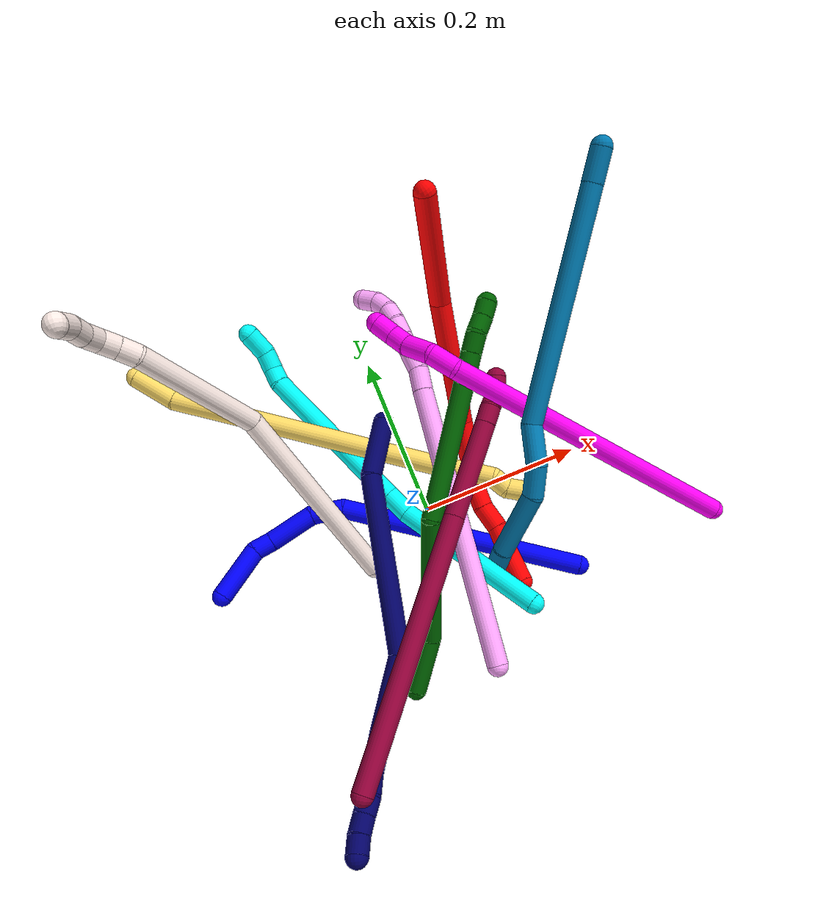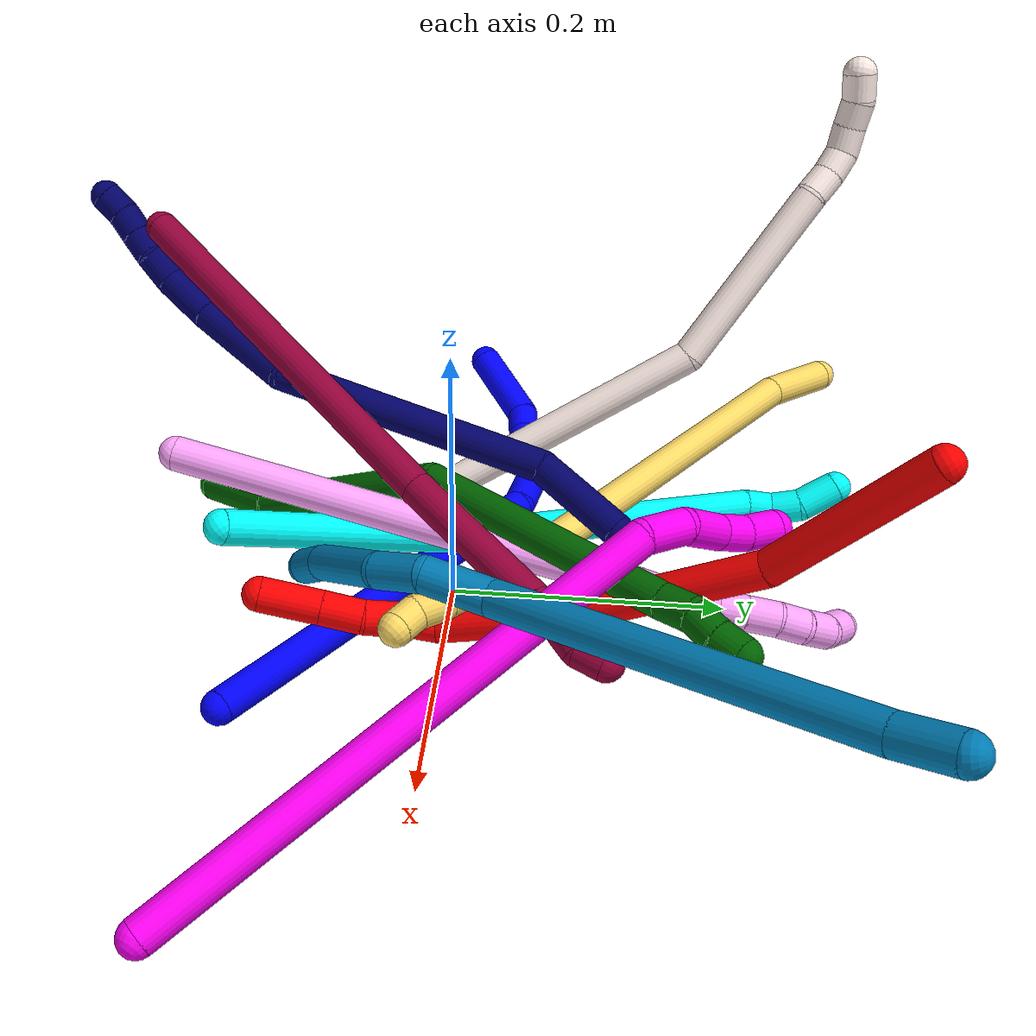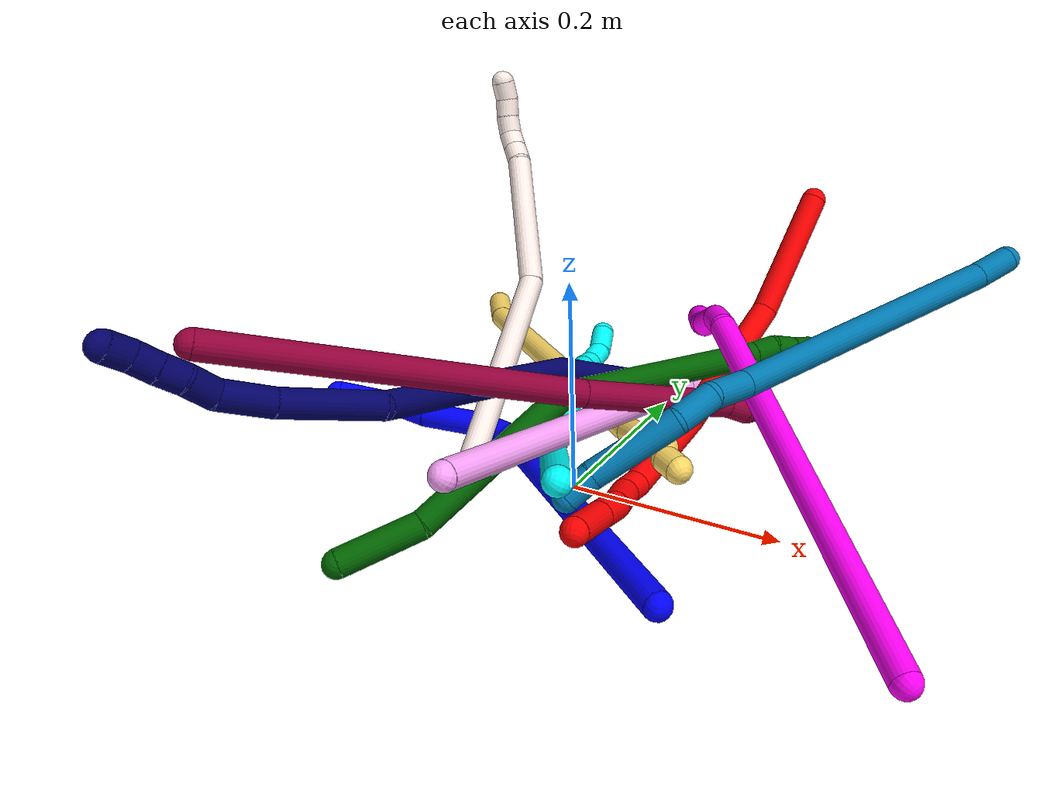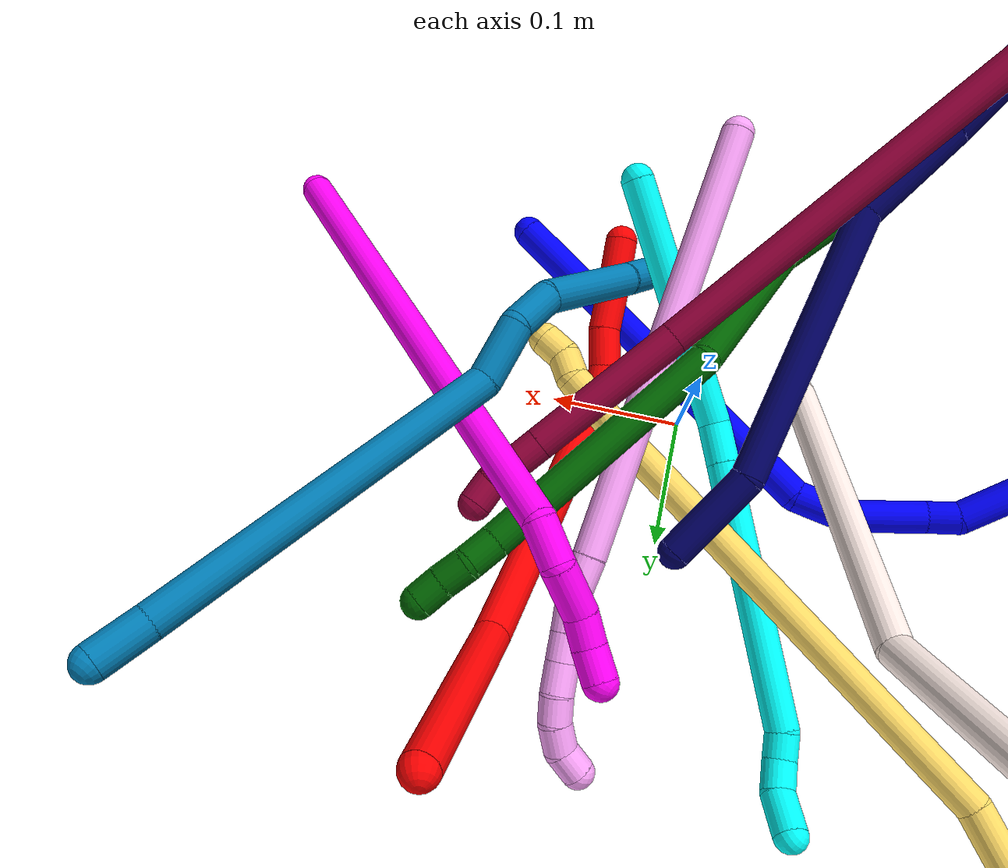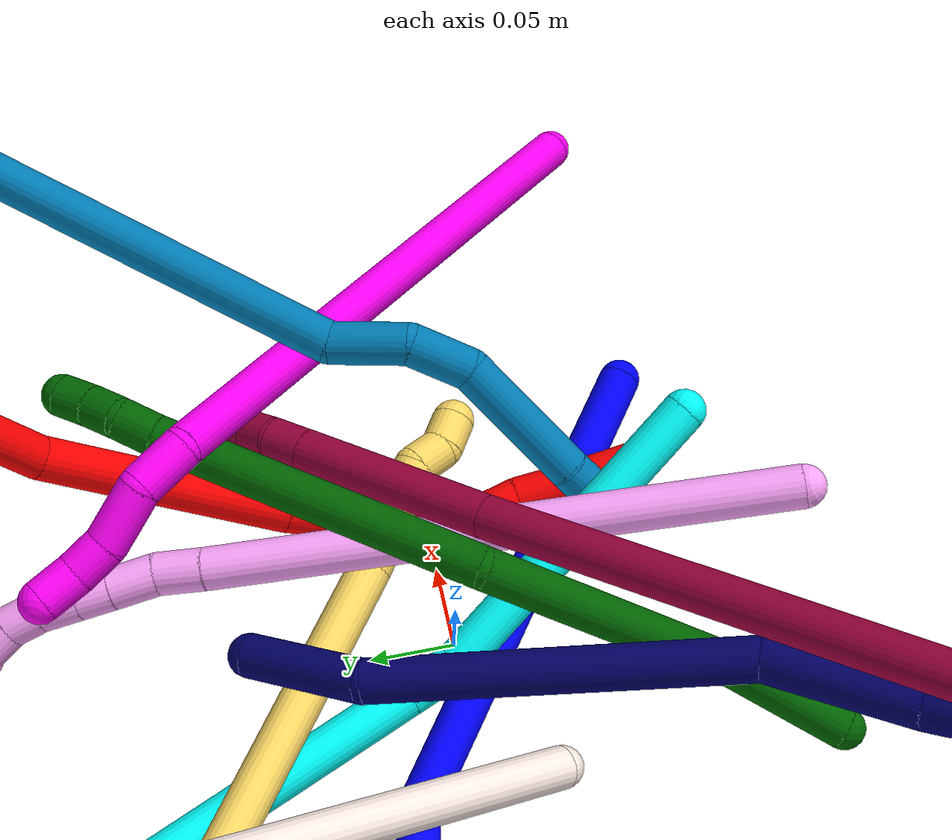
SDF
<sdf version="1.7">
 <world name="default">
  <plugin name="TubeGeneratorPlugin" filename="libtube_generator_plugin.so"/>
  <model name="photoneo_s_sensor">
   <static>1</static>
   <pose>0 0 2 1.57079 1.57079 3.14159</pose>
   <link name="link">
    <inertial><mass>0.1</mass></inertial>
    <sensor name="sensor" type="depth">
     <update_rate>30</update_rate>
     <camera>
      <horizontal_fov>1.22</horizontal_fov>
      <image><width>1920</width><height>1200</height><format>B8G8R8</format></image>
      <clip><near>0.1</near><far>4</far></clip>
      <depth_camera><output>points</output></depth_camera>
     </camera>
     <plugin name="camera_plugin" filename="libgazebo_ros_depth_camera.so">
      <baseline>0.2</baseline>
      <alwaysOn>1</alwaysOn>
      <updateRate>0.0</updateRate>
      <cameraName>camera_ir</cameraName>
      <imageTopicName>/camera/color/image_raw</imageTopicName>
      <cameraInfoTopicName>/camera/color/camera_info</cameraInfoTopicName>
      <depthImageTopicName>/camera/depth/image_raw</depthImageTopicName>
      <depthImageCameraInfoTopicName>/camera/depth/camera_info</depthImageCameraInfoTopicName>
      <pointCloudTopicName>/camera/depth/points</pointCloudTopicName>
      <frameName>fr_optical</frameName>
      <pointCloudCutoff>0.1</pointCloudCutoff>
      <pointCloudCutoffMax>2.0</pointCloudCutoffMax>
      <distortionK1>0</distortionK1>
      <distortionK2>0</distortionK2>
      <distortionK3>0</distortionK3>
      <distortionT1>0</distortionT1>
      <distortionT2>0</distortionT2>
      <CxPrime>0</CxPrime>
      <Cx>0</Cx>
      <Cy>0</Cy>
      <focalLength>0</focalLength>
      <hackBaseline>0</hackBaseline>
     </plugin>
    </sensor>
   </link>
  </model>
  <gravity>0 0 -9.8</gravity>
  <magnetic_field>6e-06 2.3e-05 -4.2e-05</magnetic_field>
  <atmosphere type="adiabatic"/>
  <physics name="default_physics" default="0" type="ode">
   <max_step_size>0.003</max_step_size>
   <real_time_factor>1</real_time_factor>
   <real_time_update_rate>1000</real_time_update_rate>
   <max_contacts>10000</max_contacts>
   <ode>
    <solver>
     <type>quick</type>
     <iters>100</iters>
     <sor>1.3</sor>
     <use_dynamic_moi_rescaling>0</use_dynamic_moi_rescaling>
    </solver>
    <constraints>
     <contact_max_correcting_vel>0</contact_max_correcting_vel>
     <contact_surface_layer>0.001</contact_surface_layer>
     <cfm>0</cfm>
     <erp>0.2</erp>
    </constraints>
   </ode>
  </physics>
  <scene><ambient>0.4 0.4 0.4 1</ambient><background>0.7 0.7 0.7 1</background><shadows>0</shadows></scene>
  <audio><device>default</device></audio>
  <spherical_coordinates>
   <surface_model>EARTH_WGS84</surface_model>
   <latitude_deg>0</latitude_deg>
   <longitude_deg>0</longitude_deg>
   <elevation>0</elevation>
   <heading_deg>0</heading_deg>
  </spherical_coordinates>
  <model name="bin">
   <static>1</static>
   <link name="bottom">
    <collision name="collision-bottom">
     <pose>0 0 -0.01 0 -0 0</pose>
     <geometry><box><size>0.8 0.6 0.02</size></box></geometry>
     <surface>
      <friction><ode><mu>100</mu><mu2>100</mu2></ode></friction>
      <contact><collide_bitmask>65535</collide_bitmask></contact>
     </surface>
    </collision>
   </link>
   <link name="west_wall">
    <collision name="collision-west_wall">
     <pose>-0.41 0 0.1 0 -0 0</pose>
     <geometry><box><size>0.02 0.6 0.2</size></box></geometry>
     <surface>
      <friction><ode><mu>100</mu><mu2>100</mu2></ode></friction>
      <contact><collide_bitmask>65535</collide_bitmask></contact>
     </surface>
    </collision>
   </link>
   <link name="east_wall">
    <collision name="collision-east_wall">
     <pose>0.41 0 0.1 0 -0 0</pose>
     <geometry><box><size>0.02 0.6 0.2</size></box></geometry>
     <surface>
      <friction><ode><mu>100</mu><mu2>100</mu2></ode></friction>
      <contact><collide_bitmask>65535</collide_bitmask></contact>
     </surface>
    </collision>
   </link>
   <link name="south_wall">
    <collision name="collision-south_wall">
     <pose>0 -0.31 0.1 0 -0 0</pose>
     <geometry><box><size>0.8 0.02 0.2</size></box></geometry>
     <surface>
      <friction><ode><mu>100</mu><mu2>100</mu2></ode></friction>
      <contact><collide_bitmask>65535</collide_bitmask></contact>
     </surface>
    </collision>
   </link>
   <link name="north_wall">
    <collision name="collision-north_wall">
     <pose>0 0.31 0.1 0 -0 0</pose>
     <geometry><box><size>0.8 0.02 0.2</size></box></geometry>
     <surface>
      <friction><ode><mu>100</mu><mu2>100</mu2></ode></friction>
      <contact><collide_bitmask>65535</collide_bitmask></contact>
     </surface>
    </collision>
   </link>
  </model>
  <model name="1">
   <static>0</static>
   <link name="1">
    <collision name="collision-cylinder-e_1_1_4">
     <pose>-0.103883 0.086547 -0.072348 -2.26707 -0.744257 1.39145</pose>
     <geometry><cylinder><radius>0.0125</radius><length>0.306699</length></cylinder></geometry>
     <surface>
      <friction><ode><mu>1.16</mu><mu2>1.16</mu2><slip1>0</slip1><slip2>0</slip2></ode></friction>
      <contact><ode><kp>1e+06</kp><kd>1</kd><max_vel>0</max_vel><min_depth>0.001</min_depth></ode></contact>
     </surface>
    </collision>
    <visual name="visual-cylinder-e_1_1_4">
     <pose>-0.103883 0.086547 -0.072348 -2.26707 -0.744257 1.39145</pose>
     <geometry><cylinder><radius>0.0125</radius><length>0.306699</length></cylinder></geometry>
     <material><ambient>0 0 1 1</ambient></material>
    </visual>
    <collision name="collision-cylinder-e_2_4_5">
     <pose>-0.225947 0.177052 -0.152843 -2.68928 -1.10852 2.42979</pose>
     <geometry><cylinder><radius>0.0125</radius><length>0.040625</length></cylinder></geometry>
     <surface>
      <friction><ode><mu>1.16</mu><mu2>1.16</mu2><slip1>0</slip1><slip2>0</slip2></ode></friction>
      <contact><ode><kp>1e+06</kp><kd>1</kd><max_vel>0</max_vel><min_depth>0.001</min_depth></ode></contact>
     </surface>
    </collision>
    <visual name="visual-cylinder-e_2_4_5">
     <pose>-0.225947 0.177052 -0.152843 -2.68928 -1.10852 2.42979</pose>
     <geometry><cylinder><radius>0.0125</radius><length>0.040625</length></cylinder></geometry>
     <material><ambient>0 0 1 1</ambient></material>
    </visual>
    <collision name="collision-cylinder-e_3_5_6">
     <pose>-0.272981 0.176731 -0.167923 2.58836 -1.29563 -2.4238</pose>
     <geometry><cylinder><radius>0.0125</radius><length>0.059963</length></cylinder></geometry>
     <surface>
      <friction><ode><mu>1.16</mu><mu2>1.16</mu2><slip1>0</slip1><slip2>0</slip2></ode></friction>
      <contact><ode><kp>1e+06</kp><kd>1</kd><max_vel>0</max_vel><min_depth>0.001</min_depth></ode></contact>
     </surface>
    </collision>
    <visual name="visual-cylinder-e_3_5_6">
     <pose>-0.272981 0.176731 -0.167923 2.58836 -1.29563 -2.4238</pose>
     <geometry><cylinder><radius>0.0125</radius><length>0.059963</length></cylinder></geometry>
     <material><ambient>0 0 1 1</ambient></material>
    </visual>
    <collision name="collision-cylinder-e_4_6_7">
     <pose>-0.313863 0.172143 -0.176282 2.92908 -1.44994 -2.90196</pose>
     <geometry><cylinder><radius>0.0125</radius><length>0.024234</length></cylinder></geometry>
     <surface>
      <friction><ode><mu>1.16</mu><mu2>1.16</mu2><slip1>0</slip1><slip2>0</slip2></ode></friction>
      <contact><ode><kp>1e+06</kp><kd>1</kd><max_vel>0</max_vel><min_depth>0.001</min_depth></ode></contact>
     </surface>
    </collision>
    <visual name="visual-cylinder-e_4_6_7">
     <pose>-0.313863 0.172143 -0.176282 2.92908 -1.44994 -2.90196</pose>
     <geometry><cylinder><radius>0.0125</radius><length>0.024234</length></cylinder></geometry>
     <material><ambient>0 0 1 1</ambient></material>
    </visual>
    <collision name="collision-cylinder-e_5_7_2">
     <pose>-0.356951 0.158446 -0.172378 1.19183 -1.13638 -0.817168</pose>
     <geometry><cylinder><radius>0.0125</radius><length>0.068478</length></cylinder></geometry>
     <surface>
      <friction><ode><mu>1.16</mu><mu2>1.16</mu2><slip1>0</slip1><slip2>0</slip2></ode></friction>
      <contact><ode><kp>1e+06</kp><kd>1</kd><max_vel>0</max_vel><min_depth>0.001</min_depth></ode></contact>
     </surface>
    </collision>
    <visual name="visual-cylinder-e_5_7_2">
     <pose>-0.356951 0.158446 -0.172378 1.19183 -1.13638 -0.817168</pose>
     <geometry><cylinder><radius>0.0125</radius><length>0.068478</length></cylinder></geometry>
     <material><ambient>0 0 1 1</ambient></material>
    </visual>
    <collision name="collision-sphere-2">
     <pose>-0.388009 0.145058 -0.167047 0 -0 0</pose>
     <geometry><sphere><radius>0.0125</radius></sphere></geometry>
     <surface>
      <friction><ode><mu>1.16</mu><mu2>1.16</mu2><slip1>0</slip1><slip2>0</slip2></ode></friction>
      <contact><ode><kp>1e+06</kp><kd>1</kd><max_vel>0</max_vel><min_depth>0.001</min_depth></ode></contact>
     </surface>
    </collision>
    <visual name="visual-sphere-2">
     <pose>-0.388009 0.145058 -0.167047 0 -0 0</pose>
     <geometry><sphere><radius>0.0125</radius></sphere></geometry>
     <material><ambient>0 0 1 1</ambient></material>
    </visual>
    <collision name="collision-sphere-7">
     <pose>-0.325892 0.171835 -0.17771 0 -0 0</pose>
     <geometry><sphere><radius>0.0125</radius></sphere></geometry>
     <surface>
      <friction><ode><mu>1.16</mu><mu2>1.16</mu2><slip1>0</slip1><slip2>0</slip2></ode></friction>
      <contact><ode><kp>1e+06</kp><kd>1</kd><max_vel>0</max_vel><min_depth>0.001</min_depth></ode></contact>
     </surface>
    </collision>
    <visual name="visual-sphere-7">
     <pose>-0.325892 0.171835 -0.17771 0 -0 0</pose>
     <geometry><sphere><radius>0.0125</radius></sphere></geometry>
     <material><ambient>0 0 1 1</ambient></material>
    </visual>
    <collision name="collision-sphere-6">
     <pose>-0.301835 0.172451 -0.174854 0 -0 0</pose>
     <geometry><sphere><radius>0.0125</radius></sphere></geometry>
     <surface>
      <friction><ode><mu>1.16</mu><mu2>1.16</mu2><slip1>0</slip1><slip2>0</slip2></ode></friction>
      <contact><ode><kp>1e+06</kp><kd>1</kd><max_vel>0</max_vel><min_depth>0.001</min_depth></ode></contact>
     </surface>
    </collision>
    <visual name="visual-sphere-6">
     <pose>-0.301835 0.172451 -0.174854 0 -0 0</pose>
     <geometry><sphere><radius>0.0125</radius></sphere></geometry>
     <material><ambient>0 0 1 1</ambient></material>
    </visual>
    <collision name="collision-sphere-5">
     <pose>-0.244127 0.181012 -0.160991 0 -0 0</pose>
     <geometry><sphere><radius>0.0125</radius></sphere></geometry>
     <surface>
      <friction><ode><mu>1.16</mu><mu2>1.16</mu2><slip1>0</slip1><slip2>0</slip2></ode></friction>
      <contact><ode><kp>1e+06</kp><kd>1</kd><max_vel>0</max_vel><min_depth>0.001</min_depth></ode></contact>
     </surface>
    </collision>
    <visual name="visual-sphere-5">
     <pose>-0.244127 0.181012 -0.160991 0 -0 0</pose>
     <geometry><sphere><radius>0.0125</radius></sphere></geometry>
     <material><ambient>0 0 1 1</ambient></material>
    </visual>
    <collision name="collision-sphere-1">
     <geometry><sphere><radius>0.0125</radius></sphere></geometry>
     <surface>
      <friction><ode><mu>1.16</mu><mu2>1.16</mu2><slip1>0</slip1><slip2>0</slip2></ode></friction>
      <contact><ode><kp>1e+06</kp><kd>1</kd><max_vel>0</max_vel><min_depth>0.001</min_depth></ode></contact>
     </surface>
    </collision>
    <visual name="visual-sphere-1">
     <geometry><sphere><radius>0.0125</radius></sphere></geometry>
     <material><ambient>0 0 1 1</ambient></material>
    </visual>
    <collision name="collision-sphere-4">
     <pose>-0.207766 0.173093 -0.144695 0 -0 0</pose>
     <geometry><sphere><radius>0.0125</radius></sphere></geometry>
     <surface>
      <friction><ode><mu>1.16</mu><mu2>1.16</mu2><slip1>0</slip1><slip2>0</slip2></ode></friction>
      <contact><ode><kp>1e+06</kp><kd>1</kd><max_vel>0</max_vel><min_depth>0.001</min_depth></ode></contact>
     </surface>
    </collision>
    <visual name="visual-sphere-4">
     <pose>-0.207766 0.173093 -0.144695 0 -0 0</pose>
     <geometry><sphere><radius>0.0125</radius></sphere></geometry>
     <material><ambient>0 0 1 1</ambient></material>
    </visual>
    <inertial>
     <pose>-0.178916 0.118712 -0.109087 0 -0 0</pose>
     <mass>0.5</mass>
     <inertia>
      <ixx>0.002027</ixx>
      <ixy>0</ixy>
      <ixz>0</ixz>
      <iyy>0.002763</iyy>
      <iyz>0</iyz>
      <izz>0.000328</izz>
     </inertia>
    </inertial>
   </link>
   <pose>0.150669 -0.138053 0.011497 0.383468 0.322485 0.149958</pose>
  </model>
  <model name="2">
   <static>0</static>
   <link name="2">
    <collision name="collision-cylinder-e_1_1_4">
     <pose>-0.027625 0.005989 -0.060037 -3.04217 -0.429371 2.69292</pose>
     <geometry><cylinder><radius>0.0125</radius><length>0.132718</length></cylinder></geometry>
     <surface>
      <friction><ode><mu>1.16</mu><mu2>1.16</mu2><slip1>0</slip1><slip2>0</slip2></ode></friction>
      <contact><ode><kp>1e+06</kp><kd>1</kd><max_vel>0</max_vel><min_depth>0.001</min_depth></ode></contact>
     </surface>
    </collision>
    <visual name="visual-cylinder-e_1_1_4">
     <pose>-0.027625 0.005989 -0.060037 -3.04217 -0.429371 2.69292</pose>
     <geometry><cylinder><radius>0.0125</radius><length>0.132718</length></cylinder></geometry>
     <material><ambient>1 0 0 1</ambient></material>
    </visual>
    <collision name="collision-cylinder-e_2_4_5">
     <pose>-0.076169 -0.003635 -0.190055 2.92208 -0.283874 -1.82777</pose>
     <geometry><cylinder><radius>0.0125</radius><length>0.149379</length></cylinder></geometry>
     <surface>
      <friction><ode><mu>1.16</mu><mu2>1.16</mu2><slip1>0</slip1><slip2>0</slip2></ode></friction>
      <contact><ode><kp>1e+06</kp><kd>1</kd><max_vel>0</max_vel><min_depth>0.001</min_depth></ode></contact>
     </surface>
    </collision>
    <visual name="visual-cylinder-e_2_4_5">
     <pose>-0.076169 -0.003635 -0.190055 2.92208 -0.283874 -1.82777</pose>
     <geometry><cylinder><radius>0.0125</radius><length>0.149379</length></cylinder></geometry>
     <material><ambient>1 0 0 1</ambient></material>
    </visual>
    <collision name="collision-cylinder-e_3_5_6">
     <pose>-0.105716 -0.035647 -0.301394 2.7641 -0.191541 -0.931925</pose>
     <geometry><cylinder><radius>0.0125</radius><length>0.090642</length></cylinder></geometry>
     <surface>
      <friction><ode><mu>1.16</mu><mu2>1.16</mu2><slip1>0</slip1><slip2>0</slip2></ode></friction>
      <contact><ode><kp>1e+06</kp><kd>1</kd><max_vel>0</max_vel><min_depth>0.001</min_depth></ode></contact>
     </surface>
    </collision>
    <visual name="visual-cylinder-e_3_5_6">
     <pose>-0.105716 -0.035647 -0.301394 2.7641 -0.191541 -0.931925</pose>
     <geometry><cylinder><radius>0.0125</radius><length>0.090642</length></cylinder></geometry>
     <material><ambient>1 0 0 1</ambient></material>
    </visual>
    <collision name="collision-cylinder-e_4_6_7">
     <pose>-0.112781 -0.059049 -0.351464 2.46452 0.13891 0.39014</pose>
     <geometry><cylinder><radius>0.0125</radius><length>0.02257</length></cylinder></geometry>
     <surface>
      <friction><ode><mu>1.16</mu><mu2>1.16</mu2><slip1>0</slip1><slip2>0</slip2></ode></friction>
      <contact><ode><kp>1e+06</kp><kd>1</kd><max_vel>0</max_vel><min_depth>0.001</min_depth></ode></contact>
     </surface>
    </collision>
    <visual name="visual-cylinder-e_4_6_7">
     <pose>-0.112781 -0.059049 -0.351464 2.46452 0.13891 0.39014</pose>
     <geometry><cylinder><radius>0.0125</radius><length>0.02257</length></cylinder></geometry>
     <material><ambient>1 0 0 1</ambient></material>
    </visual>
    <collision name="collision-cylinder-e_5_7_8">
     <pose>-0.105414 -0.074162 -0.372051 2.54239 0.383597 1.12242</pose>
     <geometry><cylinder><radius>0.0125</radius><length>0.031017</length></cylinder></geometry>
     <surface>
      <friction><ode><mu>1.16</mu><mu2>1.16</mu2><slip1>0</slip1><slip2>0</slip2></ode></friction>
      <contact><ode><kp>1e+06</kp><kd>1</kd><max_vel>0</max_vel><min_depth>0.001</min_depth></ode></contact>
     </surface>
    </collision>
    <visual name="visual-cylinder-e_5_7_8">
     <pose>-0.105414 -0.074162 -0.372051 2.54239 0.383597 1.12242</pose>
     <geometry><cylinder><radius>0.0125</radius><length>0.031017</length></cylinder></geometry>
     <material><ambient>1 0 0 1</ambient></material>
    </visual>
    <collision name="collision-cylinder-e_6_8_9">
     <pose>-0.096449 -0.092249 -0.394663 2.39288 0.212444 0.530006</pose>
     <geometry><cylinder><radius>0.0125</radius><length>0.029985</length></cylinder></geometry>
     <surface>
      <friction><ode><mu>1.16</mu><mu2>1.16</mu2><slip1>0</slip1><slip2>0</slip2></ode></friction>
      <contact><ode><kp>1e+06</kp><kd>1</kd><max_vel>0</max_vel><min_depth>0.001</min_depth></ode></contact>
     </surface>
    </collision>
    <visual name="visual-cylinder-e_6_8_9">
     <pose>-0.096449 -0.092249 -0.394663 2.39288 0.212444 0.530006</pose>
     <geometry><cylinder><radius>0.0125</radius><length>0.029985</length></cylinder></geometry>
     <material><ambient>1 0 0 1</ambient></material>
    </visual>
    <collision name="collision-cylinder-e_7_9_2">
     <pose>-0.087804 -0.116564 -0.42094 2.3964 0.253734 0.630889</pose>
     <geometry><cylinder><radius>0.0125</radius><length>0.043689</length></cylinder></geometry>
     <surface>
      <friction><ode><mu>1.16</mu><mu2>1.16</mu2><slip1>0</slip1><slip2>0</slip2></ode></friction>
      <contact><ode><kp>1e+06</kp><kd>1</kd><max_vel>0</max_vel><min_depth>0.001</min_depth></ode></contact>
     </surface>
    </collision>
    <visual name="visual-cylinder-e_7_9_2">
     <pose>-0.087804 -0.116564 -0.42094 2.3964 0.253734 0.630889</pose>
     <geometry><cylinder><radius>0.0125</radius><length>0.043689</length></cylinder></geometry>
     <material><ambient>1 0 0 1</ambient></material>
    </visual>
    <collision name="collision-sphere-2">
     <pose>-0.082321 -0.130903 -0.436481 0 -0 0</pose>
     <geometry><sphere><radius>0.0125</radius></sphere></geometry>
     <surface>
      <friction><ode><mu>1.16</mu><mu2>1.16</mu2><slip1>0</slip1><slip2>0</slip2></ode></friction>
      <contact><ode><kp>1e+06</kp><kd>1</kd><max_vel>0</max_vel><min_depth>0.001</min_depth></ode></contact>
     </surface>
    </collision>
    <visual name="visual-sphere-2">
     <pose>-0.082321 -0.130903 -0.436481 0 -0 0</pose>
     <geometry><sphere><radius>0.0125</radius></sphere></geometry>
     <material><ambient>1 0 0 1</ambient></material>
    </visual>
    <collision name="collision-sphere-9">
     <pose>-0.093287 -0.102225 -0.405399 0 -0 0</pose>
     <geometry><sphere><radius>0.0125</radius></sphere></geometry>
     <surface>
      <friction><ode><mu>1.16</mu><mu2>1.16</mu2><slip1>0</slip1><slip2>0</slip2></ode></friction>
      <contact><ode><kp>1e+06</kp><kd>1</kd><max_vel>0</max_vel><min_depth>0.001</min_depth></ode></contact>
     </surface>
    </collision>
    <visual name="visual-sphere-9">
     <pose>-0.093287 -0.102225 -0.405399 0 -0 0</pose>
     <geometry><sphere><radius>0.0125</radius></sphere></geometry>
     <material><ambient>1 0 0 1</ambient></material>
    </visual>
    <collision name="collision-sphere-4">
     <pose>-0.05525 0.011978 -0.120075 0 -0 0</pose>
     <geometry><sphere><radius>0.0125</radius></sphere></geometry>
     <surface>
      <friction><ode><mu>1.16</mu><mu2>1.16</mu2><slip1>0</slip1><slip2>0</slip2></ode></friction>
      <contact><ode><kp>1e+06</kp><kd>1</kd><max_vel>0</max_vel><min_depth>0.001</min_depth></ode></contact>
     </surface>
    </collision>
    <visual name="visual-sphere-4">
     <pose>-0.05525 0.011978 -0.120075 0 -0 0</pose>
     <geometry><sphere><radius>0.0125</radius></sphere></geometry>
     <material><ambient>1 0 0 1</ambient></material>
    </visual>
    <collision name="collision-sphere-1">
     <geometry><sphere><radius>0.0125</radius></sphere></geometry>
     <surface>
      <friction><ode><mu>1.16</mu><mu2>1.16</mu2><slip1>0</slip1><slip2>0</slip2></ode></friction>
      <contact><ode><kp>1e+06</kp><kd>1</kd><max_vel>0</max_vel><min_depth>0.001</min_depth></ode></contact>
     </surface>
    </collision>
    <visual name="visual-sphere-1">
     <geometry><sphere><radius>0.0125</radius></sphere></geometry>
     <material><ambient>1 0 0 1</ambient></material>
    </visual>
    <collision name="collision-sphere-8">
     <pose>-0.09961 -0.082273 -0.383927 0 -0 0</pose>
     <geometry><sphere><radius>0.0125</radius></sphere></geometry>
     <surface>
      <friction><ode><mu>1.16</mu><mu2>1.16</mu2><slip1>0</slip1><slip2>0</slip2></ode></friction>
      <contact><ode><kp>1e+06</kp><kd>1</kd><max_vel>0</max_vel><min_depth>0.001</min_depth></ode></contact>
     </surface>
    </collision>
    <visual name="visual-sphere-8">
     <pose>-0.09961 -0.082273 -0.383927 0 -0 0</pose>
     <geometry><sphere><radius>0.0125</radius></sphere></geometry>
     <material><ambient>1 0 0 1</ambient></material>
    </visual>
    <collision name="collision-sphere-5">
     <pose>-0.097088 -0.019248 -0.260034 0 -0 0</pose>
     <geometry><sphere><radius>0.0125</radius></sphere></geometry>
     <surface>
      <friction><ode><mu>1.16</mu><mu2>1.16</mu2><slip1>0</slip1><slip2>0</slip2></ode></friction>
      <contact><ode><kp>1e+06</kp><kd>1</kd><max_vel>0</max_vel><min_depth>0.001</min_depth></ode></contact>
     </surface>
    </collision>
    <visual name="visual-sphere-5">
     <pose>-0.097088 -0.019248 -0.260034 0 -0 0</pose>
     <geometry><sphere><radius>0.0125</radius></sphere></geometry>
     <material><ambient>1 0 0 1</ambient></material>
    </visual>
    <collision name="collision-sphere-6">
     <pose>-0.114343 -0.052047 -0.342753 0 -0 0</pose>
     <geometry><sphere><radius>0.0125</radius></sphere></geometry>
     <surface>
      <friction><ode><mu>1.16</mu><mu2>1.16</mu2><slip1>0</slip1><slip2>0</slip2></ode></friction>
      <contact><ode><kp>1e+06</kp><kd>1</kd><max_vel>0</max_vel><min_depth>0.001</min_depth></ode></contact>
     </surface>
    </collision>
    <visual name="visual-sphere-6">
     <pose>-0.114343 -0.052047 -0.342753 0 -0 0</pose>
     <geometry><sphere><radius>0.0125</radius></sphere></geometry>
     <material><ambient>1 0 0 1</ambient></material>
    </visual>
    <collision name="collision-sphere-7">
     <pose>-0.111218 -0.066051 -0.360175 0 -0 0</pose>
     <geometry><sphere><radius>0.0125</radius></sphere></geometry>
     <surface>
      <friction><ode><mu>1.16</mu><mu2>1.16</mu2><slip1>0</slip1><slip2>0</slip2></ode></friction>
      <contact><ode><kp>1e+06</kp><kd>1</kd><max_vel>0</max_vel><min_depth>0.001</min_depth></ode></contact>
     </surface>
    </collision>
    <visual name="visual-sphere-7">
     <pose>-0.111218 -0.066051 -0.360175 0 -0 0</pose>
     <geometry><sphere><radius>0.0125</radius></sphere></geometry>
     <material><ambient>1 0 0 1</ambient></material>
    </visual>
    <inertial>
     <pose>-0.07434 -0.028942 -0.226748 0 -0 0</pose>
     <mass>0.5</mass>
     <inertia>
      <ixx>-0.000414</ixx>
      <ixy>0</ixy>
      <ixz>0</ixz>
      <iyy>-7e-06</iyy>
      <iyz>0</iyz>
      <izz>0.000213</izz>
     </inertia>
    </inertial>
   </link>
   <pose>0.121817 0.301335 0.218559 -0.940984 -0.534197 -0.125945</pose>
  </model>
  <model name="3">
   <static>0</static>
   <link name="3">
    <collision name="collision-cylinder-e_1_1_4">
     <pose>-0.018549 0.08649 0.03983 -1.13923 -0.192395 0.123439</pose>
     <geometry><cylinder><radius>0.0125</radius><length>0.194021</length></cylinder></geometry>
     <surface>
      <friction><ode><mu>1.16</mu><mu2>1.16</mu2><slip1>0</slip1><slip2>0</slip2></ode></friction>
      <contact><ode><kp>1e+06</kp><kd>1</kd><max_vel>0</max_vel><min_depth>0.001</min_depth></ode></contact>
     </surface>
    </collision>
    <visual name="visual-cylinder-e_1_1_4">
     <pose>-0.018549 0.08649 0.03983 -1.13923 -0.192395 0.123439</pose>
     <geometry><cylinder><radius>0.0125</radius><length>0.194021</length></cylinder></geometry>
     <material><ambient>0.003922 1 0.996078 1</ambient></material>
    </visual>
    <collision name="collision-cylinder-e_2_4_5">
     <pose>-0.045395 0.185314 0.086216 -1.08224 -0.535985 0.327093</pose>
     <geometry><cylinder><radius>0.0125</radius><length>0.032491</length></cylinder></geometry>
     <surface>
      <friction><ode><mu>1.16</mu><mu2>1.16</mu2><slip1>0</slip1><slip2>0</slip2></ode></friction>
      <contact><ode><kp>1e+06</kp><kd>1</kd><max_vel>0</max_vel><min_depth>0.001</min_depth></ode></contact>
     </surface>
    </collision>
    <visual name="visual-cylinder-e_2_4_5">
     <pose>-0.045395 0.185314 0.086216 -1.08224 -0.535985 0.327093</pose>
     <geometry><cylinder><radius>0.0125</radius><length>0.032491</length></cylinder></geometry>
     <material><ambient>0.003922 1 0.996078 1</ambient></material>
    </visual>
    <collision name="collision-cylinder-e_3_5_6">
     <pose>-0.103942 0.273684 0.133336 -1.08073 -0.527884 0.32146</pose>
     <geometry><cylinder><radius>0.0125</radius><length>0.199521</length></cylinder></geometry>
     <surface>
      <friction><ode><mu>1.16</mu><mu2>1.16</mu2><slip1>0</slip1><slip2>0</slip2></ode></friction>
      <contact><ode><kp>1e+06</kp><kd>1</kd><max_vel>0</max_vel><min_depth>0.001</min_depth></ode></contact>
     </surface>
    </collision>
    <visual name="visual-cylinder-e_3_5_6">
     <pose>-0.103942 0.273684 0.133336 -1.08073 -0.527884 0.32146</pose>
     <geometry><cylinder><radius>0.0125</radius><length>0.199521</length></cylinder></geometry>
     <material><ambient>0.003922 1 0.996078 1</ambient></material>
    </visual>
    <collision name="collision-cylinder-e_4_6_7">
     <pose>-0.159439 0.355457 0.180464 -0.718039 -0.541822 0.207712</pose>
     <geometry><cylinder><radius>0.0125</radius><length>0.020349</length></cylinder></geometry>
     <surface>
      <friction><ode><mu>1.16</mu><mu2>1.16</mu2><slip1>0</slip1><slip2>0</slip2></ode></friction>
      <contact><ode><kp>1e+06</kp><kd>1</kd><max_vel>0</max_vel><min_depth>0.001</min_depth></ode></contact>
     </surface>
    </collision>
    <visual name="visual-cylinder-e_4_6_7">
     <pose>-0.159439 0.355457 0.180464 -0.718039 -0.541822 0.207712</pose>
     <geometry><cylinder><radius>0.0125</radius><length>0.020349</length></cylinder></geometry>
     <material><ambient>0.003922 1 0.996078 1</ambient></material>
    </visual>
    <collision name="collision-cylinder-e_5_7_8">
     <pose>-0.173731 0.365841 0.192526 -0.701974 -0.898564 0.349489</pose>
     <geometry><cylinder><radius>0.0125</radius><length>0.02312</length></cylinder></geometry>
     <surface>
      <friction><ode><mu>1.16</mu><mu2>1.16</mu2><slip1>0</slip1><slip2>0</slip2></ode></friction>
      <contact><ode><kp>1e+06</kp><kd>1</kd><max_vel>0</max_vel><min_depth>0.001</min_depth></ode></contact>
     </surface>
    </collision>
    <visual name="visual-cylinder-e_5_7_8">
     <pose>-0.173731 0.365841 0.192526 -0.701974 -0.898564 0.349489</pose>
     <geometry><cylinder><radius>0.0125</radius><length>0.02312</length></cylinder></geometry>
     <material><ambient>0.003922 1 0.996078 1</ambient></material>
    </visual>
    <collision name="collision-cylinder-e_6_8_2">
     <pose>-0.195581 0.378505 0.200091 -1.31829 -0.996896 0.798112</pose>
     <geometry><cylinder><radius>0.0125</radius><length>0.030497</length></cylinder></geometry>
     <surface>
      <friction><ode><mu>1.16</mu><mu2>1.16</mu2><slip1>0</slip1><slip2>0</slip2></ode></friction>
      <contact><ode><kp>1e+06</kp><kd>1</kd><max_vel>0</max_vel><min_depth>0.001</min_depth></ode></contact>
     </surface>
    </collision>
    <visual name="visual-cylinder-e_6_8_2">
     <pose>-0.195581 0.378505 0.200091 -1.31829 -0.996896 0.798112</pose>
     <geometry><cylinder><radius>0.0125</radius><length>0.030497</length></cylinder></geometry>
     <material><ambient>0.003922 1 0.996078 1</ambient></material>
    </visual>
    <collision name="collision-sphere-2">
     <pose>-0.208387 0.386521 0.20216 0 -0 0</pose>
     <geometry><sphere><radius>0.0125</radius></sphere></geometry>
     <surface>
      <friction><ode><mu>1.16</mu><mu2>1.16</mu2><slip1>0</slip1><slip2>0</slip2></ode></friction>
      <contact><ode><kp>1e+06</kp><kd>1</kd><max_vel>0</max_vel><min_depth>0.001</min_depth></ode></contact>
     </surface>
    </collision>
    <visual name="visual-sphere-2">
     <pose>-0.208387 0.386521 0.20216 0 -0 0</pose>
     <geometry><sphere><radius>0.0125</radius></sphere></geometry>
     <material><ambient>0.003922 1 0.996078 1</ambient></material>
    </visual>
    <collision name="collision-sphere-4">
     <pose>-0.037099 0.17298 0.07966 0 -0 0</pose>
     <geometry><sphere><radius>0.0125</radius></sphere></geometry>
     <surface>
      <friction><ode><mu>1.16</mu><mu2>1.16</mu2><slip1>0</slip1><slip2>0</slip2></ode></friction>
      <contact><ode><kp>1e+06</kp><kd>1</kd><max_vel>0</max_vel><min_depth>0.001</min_depth></ode></contact>
     </surface>
    </collision>
    <visual name="visual-sphere-4">
     <pose>-0.037099 0.17298 0.07966 0 -0 0</pose>
     <geometry><sphere><radius>0.0125</radius></sphere></geometry>
     <material><ambient>0.003922 1 0.996078 1</ambient></material>
    </visual>
    <collision name="collision-sphere-1">
     <geometry><sphere><radius>0.0125</radius></sphere></geometry>
     <surface>
      <friction><ode><mu>1.16</mu><mu2>1.16</mu2><slip1>0</slip1><slip2>0</slip2></ode></friction>
      <contact><ode><kp>1e+06</kp><kd>1</kd><max_vel>0</max_vel><min_depth>0.001</min_depth></ode></contact>
     </surface>
    </collision>
    <visual name="visual-sphere-1">
     <geometry><sphere><radius>0.0125</radius></sphere></geometry>
     <material><ambient>0.003922 1 0.996078 1</ambient></material>
    </visual>
    <collision name="collision-sphere-8">
     <pose>-0.182776 0.370489 0.198023 0 -0 0</pose>
     <geometry><sphere><radius>0.0125</radius></sphere></geometry>
     <surface>
      <friction><ode><mu>1.16</mu><mu2>1.16</mu2><slip1>0</slip1><slip2>0</slip2></ode></friction>
      <contact><ode><kp>1e+06</kp><kd>1</kd><max_vel>0</max_vel><min_depth>0.001</min_depth></ode></contact>
     </surface>
    </collision>
    <visual name="visual-sphere-8">
     <pose>-0.182776 0.370489 0.198023 0 -0 0</pose>
     <geometry><sphere><radius>0.0125</radius></sphere></geometry>
     <material><ambient>0.003922 1 0.996078 1</ambient></material>
    </visual>
    <collision name="collision-sphere-5">
     <pose>-0.053692 0.197647 0.092772 0 -0 0</pose>
     <geometry><sphere><radius>0.0125</radius></sphere></geometry>
     <surface>
      <friction><ode><mu>1.16</mu><mu2>1.16</mu2><slip1>0</slip1><slip2>0</slip2></ode></friction>
      <contact><ode><kp>1e+06</kp><kd>1</kd><max_vel>0</max_vel><min_depth>0.001</min_depth></ode></contact>
     </surface>
    </collision>
    <visual name="visual-sphere-5">
     <pose>-0.053692 0.197647 0.092772 0 -0 0</pose>
     <geometry><sphere><radius>0.0125</radius></sphere></geometry>
     <material><ambient>0.003922 1 0.996078 1</ambient></material>
    </visual>
    <collision name="collision-sphere-6">
     <pose>-0.154192 0.349722 0.173899 0 -0 0</pose>
     <geometry><sphere><radius>0.0125</radius></sphere></geometry>
     <surface>
      <friction><ode><mu>1.16</mu><mu2>1.16</mu2><slip1>0</slip1><slip2>0</slip2></ode></friction>
      <contact><ode><kp>1e+06</kp><kd>1</kd><max_vel>0</max_vel><min_depth>0.001</min_depth></ode></contact>
     </surface>
    </collision>
    <visual name="visual-sphere-6">
     <pose>-0.154192 0.349722 0.173899 0 -0 0</pose>
     <geometry><sphere><radius>0.0125</radius></sphere></geometry>
     <material><ambient>0.003922 1 0.996078 1</ambient></material>
    </visual>
    <collision name="collision-sphere-7">
     <pose>-0.164686 0.361192 0.187029 0 -0 0</pose>
     <geometry><sphere><radius>0.0125</radius></sphere></geometry>
     <surface>
      <friction><ode><mu>1.16</mu><mu2>1.16</mu2><slip1>0</slip1><slip2>0</slip2></ode></friction>
      <contact><ode><kp>1e+06</kp><kd>1</kd><max_vel>0</max_vel><min_depth>0.001</min_depth></ode></contact>
     </surface>
    </collision>
    <visual name="visual-sphere-7">
     <pose>-0.164686 0.361192 0.187029 0 -0 0</pose>
     <geometry><sphere><radius>0.0125</radius></sphere></geometry>
     <material><ambient>0.003922 1 0.996078 1</ambient></material>
    </visual>
    <inertial>
     <pose>-0.078077 0.209285 0.102716 0 -0 0</pose>
     <mass>0.5</mass>
     <inertia>
      <ixx>0.0014</ixx>
      <ixy>0</ixy>
      <ixz>0</ixz>
      <iyy>0.000961</iyy>
      <iyz>0</iyz>
      <izz>-0.000588</izz>
     </inertia>
    </inertial>
   </link>
   <pose>0.07234 -0.147559 0.101695 -2.63337 0.877196 -1.6729</pose>
  </model>
  <model name="4">
   <static>0</static>
   <link name="4">
    <collision name="collision-cylinder-e_1_1_4">
     <pose>-0.012748 0.069365 0.153652 -0.424053 -0.075476 0.016255</pose>
     <geometry><cylinder><radius>0.0125</radius><length>0.33813</length></cylinder></geometry>
     <surface>
      <friction><ode><mu>1.16</mu><mu2>1.16</mu2><slip1>0</slip1><slip2>0</slip2></ode></friction>
      <contact><ode><kp>1e+06</kp><kd>1</kd><max_vel>0</max_vel><min_depth>0.001</min_depth></ode></contact>
     </surface>
    </collision>
    <visual name="visual-cylinder-e_1_1_4">
     <pose>-0.012748 0.069365 0.153652 -0.424053 -0.075476 0.016255</pose>
     <geometry><cylinder><radius>0.0125</radius><length>0.33813</length></cylinder></geometry>
     <material><ambient>1 0.65098 0.996078 1</ambient></material>
    </visual>
    <collision name="collision-cylinder-e_2_4_5">
     <pose>-0.027036 0.143763 0.320501 -0.364344 -0.108557 0.020017</pose>
     <geometry><cylinder><radius>0.0125</radius><length>0.028415</length></cylinder></geometry>
     <surface>
      <friction><ode><mu>1.16</mu><mu2>1.16</mu2><slip1>0</slip1><slip2>0</slip2></ode></friction>
      <contact><ode><kp>1e+06</kp><kd>1</kd><max_vel>0</max_vel><min_depth>0.001</min_depth></ode></contact>
     </surface>
    </collision>
    <visual name="visual-cylinder-e_2_4_5">
     <pose>-0.027036 0.143763 0.320501 -0.364344 -0.108557 0.020017</pose>
     <geometry><cylinder><radius>0.0125</radius><length>0.028415</length></cylinder></geometry>
     <material><ambient>1 0.65098 0.996078 1</ambient></material>
    </visual>
    <collision name="collision-cylinder-e_3_5_6">
     <pose>-0.027199 0.154962 0.345914 -0.467386 0.100214 -0.023874</pose>
     <geometry><cylinder><radius>0.0125</radius><length>0.027507</length></cylinder></geometry>
     <surface>
      <friction><ode><mu>1.16</mu><mu2>1.16</mu2><slip1>0</slip1><slip2>0</slip2></ode></friction>
      <contact><ode><kp>1e+06</kp><kd>1</kd><max_vel>0</max_vel><min_depth>0.001</min_depth></ode></contact>
     </surface>
    </collision>
    <visual name="visual-cylinder-e_3_5_6">
     <pose>-0.027199 0.154962 0.345914 -0.467386 0.100214 -0.023874</pose>
     <geometry><cylinder><radius>0.0125</radius><length>0.027507</length></cylinder></geometry>
     <material><ambient>1 0.65098 0.996078 1</ambient></material>
    </visual>
    <collision name="collision-cylinder-e_4_6_7">
     <pose>-0.024951 0.165587 0.367355 -0.450349 0.084957 -0.019471</pose>
     <geometry><cylinder><radius>0.0125</radius><length>0.020565</length></cylinder></geometry>
     <surface>
      <friction><ode><mu>1.16</mu><mu2>1.16</mu2><slip1>0</slip1><slip2>0</slip2></ode></friction>
      <contact><ode><kp>1e+06</kp><kd>1</kd><max_vel>0</max_vel><min_depth>0.001</min_depth></ode></contact>
     </surface>
    </collision>
    <visual name="visual-cylinder-e_4_6_7">
     <pose>-0.024951 0.165587 0.367355 -0.450349 0.084957 -0.019471</pose>
     <geometry><cylinder><radius>0.0125</radius><length>0.020565</length></cylinder></geometry>
     <material><ambient>1 0.65098 0.996078 1</ambient></material>
    </visual>
    <collision name="collision-cylinder-e_5_7_8">
     <pose>-0.023054 0.17519 0.386886 -0.462894 0.088679 -0.020912</pose>
     <geometry><cylinder><radius>0.0125</radius><length>0.02313</length></cylinder></geometry>
     <surface>
      <friction><ode><mu>1.16</mu><mu2>1.16</mu2><slip1>0</slip1><slip2>0</slip2></ode></friction>
      <contact><ode><kp>1e+06</kp><kd>1</kd><max_vel>0</max_vel><min_depth>0.001</min_depth></ode></contact>
     </surface>
    </collision>
    <visual name="visual-cylinder-e_5_7_8">
     <pose>-0.023054 0.17519 0.386886 -0.462894 0.088679 -0.020912</pose>
     <geometry><cylinder><radius>0.0125</radius><length>0.02313</length></cylinder></geometry>
     <material><ambient>1 0.65098 0.996078 1</ambient></material>
    </visual>
    <collision name="collision-cylinder-e_6_8_9">
     <pose>-0.019518 0.183663 0.406368 -0.348027 0.251858 -0.044503</pose>
     <geometry><cylinder><radius>0.0125</radius><length>0.020155</length></cylinder></geometry>
     <surface>
      <friction><ode><mu>1.16</mu><mu2>1.16</mu2><slip1>0</slip1><slip2>0</slip2></ode></friction>
      <contact><ode><kp>1e+06</kp><kd>1</kd><max_vel>0</max_vel><min_depth>0.001</min_depth></ode></contact>
     </surface>
    </collision>
    <visual name="visual-cylinder-e_6_8_9">
     <pose>-0.019518 0.183663 0.406368 -0.348027 0.251858 -0.044503</pose>
     <geometry><cylinder><radius>0.0125</radius><length>0.020155</length></cylinder></geometry>
     <material><ambient>1 0.65098 0.996078 1</ambient></material>
    </visual>
    <collision name="collision-cylinder-e_7_9_10">
     <pose>-0.011349 0.189893 0.424257 -0.321436 0.552043 -0.091775</pose>
     <geometry><cylinder><radius>0.0125</radius><length>0.021576</length></cylinder></geometry>
     <surface>
      <friction><ode><mu>1.16</mu><mu2>1.16</mu2><slip1>0</slip1><slip2>0</slip2></ode></friction>
      <contact><ode><kp>1e+06</kp><kd>1</kd><max_vel>0</max_vel><min_depth>0.001</min_depth></ode></contact>
     </surface>
    </collision>
    <visual name="visual-cylinder-e_7_9_10">
     <pose>-0.011349 0.189893 0.424257 -0.321436 0.552043 -0.091775</pose>
     <geometry><cylinder><radius>0.0125</radius><length>0.021576</length></cylinder></geometry>
     <material><ambient>1 0.65098 0.996078 1</ambient></material>
    </visual>
    <collision name="collision-cylinder-e_8_10_2">
     <pose>0.002639 0.196011 0.438026 -0.566707 0.947391 -0.296352</pose>
     <geometry><cylinder><radius>0.0125</radius><length>0.020522</length></cylinder></geometry>
     <surface>
      <friction><ode><mu>1.16</mu><mu2>1.16</mu2><slip1>0</slip1><slip2>0</slip2></ode></friction>
      <contact><ode><kp>1e+06</kp><kd>1</kd><max_vel>0</max_vel><min_depth>0.001</min_depth></ode></contact>
     </surface>
    </collision>
    <visual name="visual-cylinder-e_8_10_2">
     <pose>0.002639 0.196011 0.438026 -0.566707 0.947391 -0.296352</pose>
     <geometry><cylinder><radius>0.0125</radius><length>0.020522</length></cylinder></geometry>
     <material><ambient>1 0.65098 0.996078 1</ambient></material>
    </visual>
    <collision name="collision-sphere-2">
     <pose>0.01097 0.199227 0.44308 0 -0 0</pose>
     <geometry><sphere><radius>0.0125</radius></sphere></geometry>
     <surface>
      <friction><ode><mu>1.16</mu><mu2>1.16</mu2><slip1>0</slip1><slip2>0</slip2></ode></friction>
      <contact><ode><kp>1e+06</kp><kd>1</kd><max_vel>0</max_vel><min_depth>0.001</min_depth></ode></contact>
     </surface>
    </collision>
    <visual name="visual-sphere-2">
     <pose>0.01097 0.199227 0.44308 0 -0 0</pose>
     <geometry><sphere><radius>0.0125</radius></sphere></geometry>
     <material><ambient>1 0.65098 0.996078 1</ambient></material>
    </visual>
    <collision name="collision-sphere-10">
     <pose>-0.005692 0.192795 0.432972 0 -0 0</pose>
     <geometry><sphere><radius>0.0125</radius></sphere></geometry>
     <surface>
      <friction><ode><mu>1.16</mu><mu2>1.16</mu2><slip1>0</slip1><slip2>0</slip2></ode></friction>
      <contact><ode><kp>1e+06</kp><kd>1</kd><max_vel>0</max_vel><min_depth>0.001</min_depth></ode></contact>
     </surface>
    </collision>
    <visual name="visual-sphere-10">
     <pose>-0.005692 0.192795 0.432972 0 -0 0</pose>
     <geometry><sphere><radius>0.0125</radius></sphere></geometry>
     <material><ambient>1 0.65098 0.996078 1</ambient></material>
    </visual>
    <collision name="collision-sphere-9">
     <pose>-0.017007 0.186991 0.415542 0 -0 0</pose>
     <geometry><sphere><radius>0.0125</radius></sphere></geometry>
     <surface>
      <friction><ode><mu>1.16</mu><mu2>1.16</mu2><slip1>0</slip1><slip2>0</slip2></ode></friction>
      <contact><ode><kp>1e+06</kp><kd>1</kd><max_vel>0</max_vel><min_depth>0.001</min_depth></ode></contact>
     </surface>
    </collision>
    <visual name="visual-sphere-9">
     <pose>-0.017007 0.186991 0.415542 0 -0 0</pose>
     <geometry><sphere><radius>0.0125</radius></sphere></geometry>
     <material><ambient>1 0.65098 0.996078 1</ambient></material>
    </visual>
    <collision name="collision-sphere-4">
     <pose>-0.025497 0.13873 0.307304 0 -0 0</pose>
     <geometry><sphere><radius>0.0125</radius></sphere></geometry>
     <surface>
      <friction><ode><mu>1.16</mu><mu2>1.16</mu2><slip1>0</slip1><slip2>0</slip2></ode></friction>
      <contact><ode><kp>1e+06</kp><kd>1</kd><max_vel>0</max_vel><min_depth>0.001</min_depth></ode></contact>
     </surface>
    </collision>
    <visual name="visual-sphere-4">
     <pose>-0.025497 0.13873 0.307304 0 -0 0</pose>
     <geometry><sphere><radius>0.0125</radius></sphere></geometry>
     <material><ambient>1 0.65098 0.996078 1</ambient></material>
    </visual>
    <collision name="collision-sphere-1">
     <geometry><sphere><radius>0.0125</radius></sphere></geometry>
     <surface>
      <friction><ode><mu>1.16</mu><mu2>1.16</mu2><slip1>0</slip1><slip2>0</slip2></ode></friction>
      <contact><ode><kp>1e+06</kp><kd>1</kd><max_vel>0</max_vel><min_depth>0.001</min_depth></ode></contact>
     </surface>
    </collision>
    <visual name="visual-sphere-1">
     <geometry><sphere><radius>0.0125</radius></sphere></geometry>
     <material><ambient>1 0.65098 0.996078 1</ambient></material>
    </visual>
    <collision name="collision-sphere-8">
     <pose>-0.02203 0.180334 0.397194 0 -0 0</pose>
     <geometry><sphere><radius>0.0125</radius></sphere></geometry>
     <surface>
      <friction><ode><mu>1.16</mu><mu2>1.16</mu2><slip1>0</slip1><slip2>0</slip2></ode></friction>
      <contact><ode><kp>1e+06</kp><kd>1</kd><max_vel>0</max_vel><min_depth>0.001</min_depth></ode></contact>
     </surface>
    </collision>
    <visual name="visual-sphere-8">
     <pose>-0.02203 0.180334 0.397194 0 -0 0</pose>
     <geometry><sphere><radius>0.0125</radius></sphere></geometry>
     <material><ambient>1 0.65098 0.996078 1</ambient></material>
    </visual>
    <collision name="collision-sphere-5">
     <pose>-0.028575 0.148796 0.333698 0 -0 0</pose>
     <geometry><sphere><radius>0.0125</radius></sphere></geometry>
     <surface>
      <friction><ode><mu>1.16</mu><mu2>1.16</mu2><slip1>0</slip1><slip2>0</slip2></ode></friction>
      <contact><ode><kp>1e+06</kp><kd>1</kd><max_vel>0</max_vel><min_depth>0.001</min_depth></ode></contact>
     </surface>
    </collision>
    <visual name="visual-sphere-5">
     <pose>-0.028575 0.148796 0.333698 0 -0 0</pose>
     <geometry><sphere><radius>0.0125</radius></sphere></geometry>
     <material><ambient>1 0.65098 0.996078 1</ambient></material>
    </visual>
    <collision name="collision-sphere-6">
     <pose>-0.025823 0.161127 0.358131 0 -0 0</pose>
     <geometry><sphere><radius>0.0125</radius></sphere></geometry>
     <surface>
      <friction><ode><mu>1.16</mu><mu2>1.16</mu2><slip1>0</slip1><slip2>0</slip2></ode></friction>
      <contact><ode><kp>1e+06</kp><kd>1</kd><max_vel>0</max_vel><min_depth>0.001</min_depth></ode></contact>
     </surface>
    </collision>
    <visual name="visual-sphere-6">
     <pose>-0.025823 0.161127 0.358131 0 -0 0</pose>
     <geometry><sphere><radius>0.0125</radius></sphere></geometry>
     <material><ambient>1 0.65098 0.996078 1</ambient></material>
    </visual>
    <collision name="collision-sphere-7">
     <pose>-0.024078 0.170046 0.376579 0 -0 0</pose>
     <geometry><sphere><radius>0.0125</radius></sphere></geometry>
     <surface>
      <friction><ode><mu>1.16</mu><mu2>1.16</mu2><slip1>0</slip1><slip2>0</slip2></ode></friction>
      <contact><ode><kp>1e+06</kp><kd>1</kd><max_vel>0</max_vel><min_depth>0.001</min_depth></ode></contact>
     </surface>
    </collision>
    <visual name="visual-sphere-7">
     <pose>-0.024078 0.170046 0.376579 0 -0 0</pose>
     <geometry><sphere><radius>0.0125</radius></sphere></geometry>
     <material><ambient>1 0.65098 0.996078 1</ambient></material>
    </visual>
    <inertial>
     <pose>-0.014915 0.102162 0.226826 0 -0 0</pose>
     <mass>0.5</mass>
     <inertia>
      <ixx>0.003291</ixx>
      <ixy>0</ixy>
      <ixz>0</ixz>
      <iyy>0.00303</iyy>
      <iyz>0</iyz>
      <izz>-0.001057</izz>
     </inertia>
    </inertial>
   </link>
   <pose>0.006347 -0.195965 0.113918 2.21413 0.421819 -3.11217</pose>
  </model>
  <model name="5">
   <static>0</static>
   <link name="5">
    <collision name="collision-cylinder-e_1_1_4">
     <pose>0.002869 -0.010849 -0.024515 2.72496 0.106606 0.494481</pose>
     <geometry><cylinder><radius>0.0125</radius><length>0.053923</length></cylinder></geometry>
     <surface>
      <friction><ode><mu>1.16</mu><mu2>1.16</mu2><slip1>0</slip1><slip2>0</slip2></ode></friction>
      <contact><ode><kp>1e+06</kp><kd>1</kd><max_vel>0</max_vel><min_depth>0.001</min_depth></ode></contact>
     </surface>
    </collision>
    <visual name="visual-cylinder-e_1_1_4">
     <pose>0.002869 -0.010849 -0.024515 2.72496 0.106606 0.494481</pose>
     <geometry><cylinder><radius>0.0125</radius><length>0.053923</length></cylinder></geometry>
     <material><ambient>1 0.858824 0.4 1</ambient></material>
    </visual>
    <collision name="collision-cylinder-e_2_4_5">
     <pose>0.056662 -0.052415 -0.207655 2.95032 0.305327 2.02656</pose>
     <geometry><cylinder><radius>0.0125</radius><length>0.338814</length></cylinder></geometry>
     <surface>
      <friction><ode><mu>1.16</mu><mu2>1.16</mu2><slip1>0</slip1><slip2>0</slip2></ode></friction>
      <contact><ode><kp>1e+06</kp><kd>1</kd><max_vel>0</max_vel><min_depth>0.001</min_depth></ode></contact>
     </surface>
    </collision>
    <visual name="visual-cylinder-e_2_4_5">
     <pose>0.056662 -0.052415 -0.207655 2.95032 0.305327 2.02656</pose>
     <geometry><cylinder><radius>0.0125</radius><length>0.338814</length></cylinder></geometry>
     <material><ambient>1 0.858824 0.4 1</ambient></material>
    </visual>
    <collision name="collision-cylinder-e_3_5_6">
     <pose>0.113026 -0.086554 -0.377746 2.8515 0.426626 1.95496</pose>
     <geometry><cylinder><radius>0.0125</radius><length>0.026288</length></cylinder></geometry>
     <surface>
      <friction><ode><mu>1.16</mu><mu2>1.16</mu2><slip1>0</slip1><slip2>0</slip2></ode></friction>
      <contact><ode><kp>1e+06</kp><kd>1</kd><max_vel>0</max_vel><min_depth>0.001</min_depth></ode></contact>
     </surface>
    </collision>
    <visual name="visual-cylinder-e_3_5_6">
     <pose>0.113026 -0.086554 -0.377746 2.8515 0.426626 1.95496</pose>
     <geometry><cylinder><radius>0.0125</radius><length>0.026288</length></cylinder></geometry>
     <material><ambient>1 0.858824 0.4 1</ambient></material>
    </visual>
    <collision name="collision-cylinder-e_4_6_7">
     <pose>0.124408 -0.093535 -0.396741 2.70015 0.619848 1.91928</pose>
     <geometry><cylinder><radius>0.0125</radius><length>0.020462</length></cylinder></geometry>
     <surface>
      <friction><ode><mu>1.16</mu><mu2>1.16</mu2><slip1>0</slip1><slip2>0</slip2></ode></friction>
      <contact><ode><kp>1e+06</kp><kd>1</kd><max_vel>0</max_vel><min_depth>0.001</min_depth></ode></contact>
     </surface>
    </collision>
    <visual name="visual-cylinder-e_4_6_7">
     <pose>0.124408 -0.093535 -0.396741 2.70015 0.619848 1.91928</pose>
     <geometry><cylinder><radius>0.0125</radius><length>0.020462</length></cylinder></geometry>
     <material><ambient>1 0.858824 0.4 1</ambient></material>
    </visual>
    <collision name="collision-cylinder-e_5_7_8">
     <pose>0.134377 -0.099634 -0.413257 2.86594 0.407003 1.95799</pose>
     <geometry><cylinder><radius>0.0125</radius><length>0.020339</length></cylinder></geometry>
     <surface>
      <friction><ode><mu>1.16</mu><mu2>1.16</mu2><slip1>0</slip1><slip2>0</slip2></ode></friction>
      <contact><ode><kp>1e+06</kp><kd>1</kd><max_vel>0</max_vel><min_depth>0.001</min_depth></ode></contact>
     </surface>
    </collision>
    <visual name="visual-cylinder-e_5_7_8">
     <pose>0.134377 -0.099634 -0.413257 2.86594 0.407003 1.95799</pose>
     <geometry><cylinder><radius>0.0125</radius><length>0.020339</length></cylinder></geometry>
     <material><ambient>1 0.858824 0.4 1</ambient></material>
    </visual>
    <collision name="collision-cylinder-e_6_8_9">
     <pose>0.13779 -0.10652 -0.431319 2.69524 -0.060816 -0.266459</pose>
     <geometry><cylinder><radius>0.0125</radius><length>0.02016</length></cylinder></geometry>
     <surface>
      <friction><ode><mu>1.16</mu><mu2>1.16</mu2><slip1>0</slip1><slip2>0</slip2></ode></friction>
      <contact><ode><kp>1e+06</kp><kd>1</kd><max_vel>0</max_vel><min_depth>0.001</min_depth></ode></contact>
     </surface>
    </collision>
    <visual name="visual-cylinder-e_6_8_9">
     <pose>0.13779 -0.10652 -0.431319 2.69524 -0.060816 -0.266459</pose>
     <geometry><cylinder><radius>0.0125</radius><length>0.02016</length></cylinder></geometry>
     <material><ambient>1 0.858824 0.4 1</ambient></material>
    </visual>
    <collision name="collision-cylinder-e_7_9_2">
     <pose>0.140411 -0.111891 -0.449809 3.03279 0.329066 2.50773</pose>
     <geometry><cylinder><radius>0.0125</radius><length>0.020014</length></cylinder></geometry>
     <surface>
      <friction><ode><mu>1.16</mu><mu2>1.16</mu2><slip1>0</slip1><slip2>0</slip2></ode></friction>
      <contact><ode><kp>1e+06</kp><kd>1</kd><max_vel>0</max_vel><min_depth>0.001</min_depth></ode></contact>
     </surface>
    </collision>
    <visual name="visual-cylinder-e_7_9_2">
     <pose>0.140411 -0.111891 -0.449809 3.03279 0.329066 2.50773</pose>
     <geometry><cylinder><radius>0.0125</radius><length>0.020014</length></cylinder></geometry>
     <material><ambient>1 0.858824 0.4 1</ambient></material>
    </visual>
    <collision name="collision-sphere-2">
     <pose>0.143645 -0.11292 -0.459223 0 -0 0</pose>
     <geometry><sphere><radius>0.0125</radius></sphere></geometry>
     <surface>
      <friction><ode><mu>1.16</mu><mu2>1.16</mu2><slip1>0</slip1><slip2>0</slip2></ode></friction>
      <contact><ode><kp>1e+06</kp><kd>1</kd><max_vel>0</max_vel><min_depth>0.001</min_depth></ode></contact>
     </surface>
    </collision>
    <visual name="visual-sphere-2">
     <pose>0.143645 -0.11292 -0.459223 0 -0 0</pose>
     <geometry><sphere><radius>0.0125</radius></sphere></geometry>
     <material><ambient>1 0.858824 0.4 1</ambient></material>
    </visual>
    <collision name="collision-sphere-9">
     <pose>0.137177 -0.110863 -0.440394 0 -0 0</pose>
     <geometry><sphere><radius>0.0125</radius></sphere></geometry>
     <surface>
      <friction><ode><mu>1.16</mu><mu2>1.16</mu2><slip1>0</slip1><slip2>0</slip2></ode></friction>
      <contact><ode><kp>1e+06</kp><kd>1</kd><max_vel>0</max_vel><min_depth>0.001</min_depth></ode></contact>
     </surface>
    </collision>
    <visual name="visual-sphere-9">
     <pose>0.137177 -0.110863 -0.440394 0 -0 0</pose>
     <geometry><sphere><radius>0.0125</radius></sphere></geometry>
     <material><ambient>1 0.858824 0.4 1</ambient></material>
    </visual>
    <collision name="collision-sphere-4">
     <pose>0.005738 -0.021698 -0.04903 0 -0 0</pose>
     <geometry><sphere><radius>0.0125</radius></sphere></geometry>
     <surface>
      <friction><ode><mu>1.16</mu><mu2>1.16</mu2><slip1>0</slip1><slip2>0</slip2></ode></friction>
      <contact><ode><kp>1e+06</kp><kd>1</kd><max_vel>0</max_vel><min_depth>0.001</min_depth></ode></contact>
     </surface>
    </collision>
    <visual name="visual-sphere-4">
     <pose>0.005738 -0.021698 -0.04903 0 -0 0</pose>
     <geometry><sphere><radius>0.0125</radius></sphere></geometry>
     <material><ambient>1 0.858824 0.4 1</ambient></material>
    </visual>
    <collision name="collision-sphere-1">
     <geometry><sphere><radius>0.0125</radius></sphere></geometry>
     <surface>
      <friction><ode><mu>1.16</mu><mu2>1.16</mu2><slip1>0</slip1><slip2>0</slip2></ode></friction>
      <contact><ode><kp>1e+06</kp><kd>1</kd><max_vel>0</max_vel><min_depth>0.001</min_depth></ode></contact>
     </surface>
    </collision>
    <visual name="visual-sphere-1">
     <geometry><sphere><radius>0.0125</radius></sphere></geometry>
     <material><ambient>1 0.858824 0.4 1</ambient></material>
    </visual>
    <collision name="collision-sphere-8">
     <pose>0.138403 -0.102176 -0.422243 0 -0 0</pose>
     <geometry><sphere><radius>0.0125</radius></sphere></geometry>
     <surface>
      <friction><ode><mu>1.16</mu><mu2>1.16</mu2><slip1>0</slip1><slip2>0</slip2></ode></friction>
      <contact><ode><kp>1e+06</kp><kd>1</kd><max_vel>0</max_vel><min_depth>0.001</min_depth></ode></contact>
     </surface>
    </collision>
    <visual name="visual-sphere-8">
     <pose>0.138403 -0.102176 -0.422243 0 -0 0</pose>
     <geometry><sphere><radius>0.0125</radius></sphere></geometry>
     <material><ambient>1 0.858824 0.4 1</ambient></material>
    </visual>
    <collision name="collision-sphere-5">
     <pose>0.107587 -0.083131 -0.36628 0 -0 0</pose>
     <geometry><sphere><radius>0.0125</radius></sphere></geometry>
     <surface>
      <friction><ode><mu>1.16</mu><mu2>1.16</mu2><slip1>0</slip1><slip2>0</slip2></ode></friction>
      <contact><ode><kp>1e+06</kp><kd>1</kd><max_vel>0</max_vel><min_depth>0.001</min_depth></ode></contact>
     </surface>
    </collision>
    <visual name="visual-sphere-5">
     <pose>0.107587 -0.083131 -0.36628 0 -0 0</pose>
     <geometry><sphere><radius>0.0125</radius></sphere></geometry>
     <material><ambient>1 0.858824 0.4 1</ambient></material>
    </visual>
    <collision name="collision-sphere-6">
     <pose>0.118465 -0.089977 -0.389212 0 -0 0</pose>
     <geometry><sphere><radius>0.0125</radius></sphere></geometry>
     <surface>
      <friction><ode><mu>1.16</mu><mu2>1.16</mu2><slip1>0</slip1><slip2>0</slip2></ode></friction>
      <contact><ode><kp>1e+06</kp><kd>1</kd><max_vel>0</max_vel><min_depth>0.001</min_depth></ode></contact>
     </surface>
    </collision>
    <visual name="visual-sphere-6">
     <pose>0.118465 -0.089977 -0.389212 0 -0 0</pose>
     <geometry><sphere><radius>0.0125</radius></sphere></geometry>
     <material><ambient>1 0.858824 0.4 1</ambient></material>
    </visual>
    <collision name="collision-sphere-7">
     <pose>0.130351 -0.097093 -0.404271 0 -0 0</pose>
     <geometry><sphere><radius>0.0125</radius></sphere></geometry>
     <surface>
      <friction><ode><mu>1.16</mu><mu2>1.16</mu2><slip1>0</slip1><slip2>0</slip2></ode></friction>
      <contact><ode><kp>1e+06</kp><kd>1</kd><max_vel>0</max_vel><min_depth>0.001</min_depth></ode></contact>
     </surface>
    </collision>
    <visual name="visual-sphere-7">
     <pose>0.130351 -0.097093 -0.404271 0 -0 0</pose>
     <geometry><sphere><radius>0.0125</radius></sphere></geometry>
     <material><ambient>1 0.858824 0.4 1</ambient></material>
    </visual>
    <inertial>
     <pose>0.066381 -0.057893 -0.23166 0 -0 0</pose>
     <mass>0.5</mass>
     <inertia>
      <ixx>0.001456</ixx>
      <ixy>0</ixy>
      <ixz>0</ixz>
      <iyy>0.004354</iyy>
      <iyz>0</iyz>
      <izz>-0.00042</izz>
     </inertia>
    </inertial>
   </link>
   <pose>-0.269453 0.286688 0.044842 -1.03943 -0.832587 0.483089</pose>
  </model>
  <model name="6">
   <static>0</static>
   <link name="6">
    <collision name="collision-cylinder-e_1_1_4">
     <pose>0.018389 0.029002 0.010092 -1.23593 0.539581 -0.388193</pose>
     <geometry><cylinder><radius>0.0125</radius><length>0.071585</length></cylinder></geometry>
     <surface>
      <friction><ode><mu>1.16</mu><mu2>1.16</mu2><slip1>0</slip1><slip2>0</slip2></ode></friction>
      <contact><ode><kp>1e+06</kp><kd>1</kd><max_vel>0</max_vel><min_depth>0.001</min_depth></ode></contact>
     </surface>
    </collision>
    <visual name="visual-cylinder-e_1_1_4">
     <pose>0.018389 0.029002 0.010092 -1.23593 0.539581 -0.388193</pose>
     <geometry><cylinder><radius>0.0125</radius><length>0.071585</length></cylinder></geometry>
     <material><ambient>0 0.392157 0.003922 1</ambient></material>
    </visual>
    <collision name="collision-cylinder-e_2_4_5">
     <pose>0.054047 0.134157 0.043635 -1.27206 0.213412 -0.157853</pose>
     <geometry><cylinder><radius>0.0125</radius><length>0.163064</length></cylinder></geometry>
     <surface>
      <friction><ode><mu>1.16</mu><mu2>1.16</mu2><slip1>0</slip1><slip2>0</slip2></ode></friction>
      <contact><ode><kp>1e+06</kp><kd>1</kd><max_vel>0</max_vel><min_depth>0.001</min_depth></ode></contact>
     </surface>
    </collision>
    <visual name="visual-cylinder-e_2_4_5">
     <pose>0.054047 0.134157 0.043635 -1.27206 0.213412 -0.157853</pose>
     <geometry><cylinder><radius>0.0125</radius><length>0.163064</length></cylinder></geometry>
     <material><ambient>0 0.392157 0.003922 1</ambient></material>
    </visual>
    <collision name="collision-cylinder-e_3_5_6">
     <pose>0.134807 0.287483 0.075548 -1.4616 0.685508 -0.619145</pose>
     <geometry><cylinder><radius>0.0125</radius><length>0.200583</length></cylinder></geometry>
     <surface>
      <friction><ode><mu>1.16</mu><mu2>1.16</mu2><slip1>0</slip1><slip2>0</slip2></ode></friction>
      <contact><ode><kp>1e+06</kp><kd>1</kd><max_vel>0</max_vel><min_depth>0.001</min_depth></ode></contact>
     </surface>
    </collision>
    <visual name="visual-cylinder-e_3_5_6">
     <pose>0.134807 0.287483 0.075548 -1.4616 0.685508 -0.619145</pose>
     <geometry><cylinder><radius>0.0125</radius><length>0.200583</length></cylinder></geometry>
     <material><ambient>0 0.392157 0.003922 1</ambient></material>
    </visual>
    <collision name="collision-cylinder-e_4_6_7">
     <pose>0.205214 0.374075 0.086124 -1.34986 0.621671 -0.503298</pose>
     <geometry><cylinder><radius>0.0125</radius><length>0.02375</length></cylinder></geometry>
     <surface>
      <friction><ode><mu>1.16</mu><mu2>1.16</mu2><slip1>0</slip1><slip2>0</slip2></ode></friction>
      <contact><ode><kp>1e+06</kp><kd>1</kd><max_vel>0</max_vel><min_depth>0.001</min_depth></ode></contact>
     </surface>
    </collision>
    <visual name="visual-cylinder-e_4_6_7">
     <pose>0.205214 0.374075 0.086124 -1.34986 0.621671 -0.503298</pose>
     <geometry><cylinder><radius>0.0125</radius><length>0.02375</length></cylinder></geometry>
     <material><ambient>0 0.392157 0.003922 1</ambient></material>
    </visual>
    <collision name="collision-cylinder-e_5_7_8">
     <pose>0.220555 0.389705 0.088068 -1.59827 0.935306 -0.957602</pose>
     <geometry><cylinder><radius>0.0125</radius><length>0.020937</length></cylinder></geometry>
     <surface>
      <friction><ode><mu>1.16</mu><mu2>1.16</mu2><slip1>0</slip1><slip2>0</slip2></ode></friction>
      <contact><ode><kp>1e+06</kp><kd>1</kd><max_vel>0</max_vel><min_depth>0.001</min_depth></ode></contact>
     </surface>
    </collision>
    <visual name="visual-cylinder-e_5_7_8">
     <pose>0.220555 0.389705 0.088068 -1.59827 0.935306 -0.957602</pose>
     <geometry><cylinder><radius>0.0125</radius><length>0.020937</length></cylinder></geometry>
     <material><ambient>0 0.392157 0.003922 1</ambient></material>
    </visual>
    <collision name="collision-cylinder-e_6_8_2">
     <pose>0.236308 0.402778 0.087773 -1.58891 0.818248 -0.831555</pose>
     <geometry><cylinder><radius>0.0125</radius><length>0.020079</length></cylinder></geometry>
     <surface>
      <friction><ode><mu>1.16</mu><mu2>1.16</mu2><slip1>0</slip1><slip2>0</slip2></ode></friction>
      <contact><ode><kp>1e+06</kp><kd>1</kd><max_vel>0</max_vel><min_depth>0.001</min_depth></ode></contact>
     </surface>
    </collision>
    <visual name="visual-cylinder-e_6_8_2">
     <pose>0.236308 0.402778 0.087773 -1.58891 0.818248 -0.831555</pose>
     <geometry><cylinder><radius>0.0125</radius><length>0.020079</length></cylinder></geometry>
     <material><ambient>0 0.392157 0.003922 1</ambient></material>
    </visual>
    <collision name="collision-sphere-2">
     <pose>0.243637 0.409639 0.087649 0 -0 0</pose>
     <geometry><sphere><radius>0.0125</radius></sphere></geometry>
     <surface>
      <friction><ode><mu>1.16</mu><mu2>1.16</mu2><slip1>0</slip1><slip2>0</slip2></ode></friction>
      <contact><ode><kp>1e+06</kp><kd>1</kd><max_vel>0</max_vel><min_depth>0.001</min_depth></ode></contact>
     </surface>
    </collision>
    <visual name="visual-sphere-2">
     <pose>0.243637 0.409639 0.087649 0 -0 0</pose>
     <geometry><sphere><radius>0.0125</radius></sphere></geometry>
     <material><ambient>0 0.392157 0.003922 1</ambient></material>
    </visual>
    <collision name="collision-sphere-4">
     <pose>0.036779 0.058004 0.020183 0 -0 0</pose>
     <geometry><sphere><radius>0.0125</radius></sphere></geometry>
     <surface>
      <friction><ode><mu>1.16</mu><mu2>1.16</mu2><slip1>0</slip1><slip2>0</slip2></ode></friction>
      <contact><ode><kp>1e+06</kp><kd>1</kd><max_vel>0</max_vel><min_depth>0.001</min_depth></ode></contact>
     </surface>
    </collision>
    <visual name="visual-sphere-4">
     <pose>0.036779 0.058004 0.020183 0 -0 0</pose>
     <geometry><sphere><radius>0.0125</radius></sphere></geometry>
     <material><ambient>0 0.392157 0.003922 1</ambient></material>
    </visual>
    <collision name="collision-sphere-1">
     <geometry><sphere><radius>0.0125</radius></sphere></geometry>
     <surface>
      <friction><ode><mu>1.16</mu><mu2>1.16</mu2><slip1>0</slip1><slip2>0</slip2></ode></friction>
      <contact><ode><kp>1e+06</kp><kd>1</kd><max_vel>0</max_vel><min_depth>0.001</min_depth></ode></contact>
     </surface>
    </collision>
    <visual name="visual-sphere-1">
     <geometry><sphere><radius>0.0125</radius></sphere></geometry>
     <material><ambient>0 0.392157 0.003922 1</ambient></material>
    </visual>
    <collision name="collision-sphere-8">
     <pose>0.22898 0.395917 0.087898 0 -0 0</pose>
     <geometry><sphere><radius>0.0125</radius></sphere></geometry>
     <surface>
      <friction><ode><mu>1.16</mu><mu2>1.16</mu2><slip1>0</slip1><slip2>0</slip2></ode></friction>
      <contact><ode><kp>1e+06</kp><kd>1</kd><max_vel>0</max_vel><min_depth>0.001</min_depth></ode></contact>
     </surface>
    </collision>
    <visual name="visual-sphere-8">
     <pose>0.22898 0.395917 0.087898 0 -0 0</pose>
     <geometry><sphere><radius>0.0125</radius></sphere></geometry>
     <material><ambient>0 0.392157 0.003922 1</ambient></material>
    </visual>
    <collision name="collision-sphere-5">
     <pose>0.071315 0.21031 0.067087 0 -0 0</pose>
     <geometry><sphere><radius>0.0125</radius></sphere></geometry>
     <surface>
      <friction><ode><mu>1.16</mu><mu2>1.16</mu2><slip1>0</slip1><slip2>0</slip2></ode></friction>
      <contact><ode><kp>1e+06</kp><kd>1</kd><max_vel>0</max_vel><min_depth>0.001</min_depth></ode></contact>
     </surface>
    </collision>
    <visual name="visual-sphere-5">
     <pose>0.071315 0.21031 0.067087 0 -0 0</pose>
     <geometry><sphere><radius>0.0125</radius></sphere></geometry>
     <material><ambient>0 0.392157 0.003922 1</ambient></material>
    </visual>
    <collision name="collision-sphere-6">
     <pose>0.198298 0.364656 0.084008 0 -0 0</pose>
     <geometry><sphere><radius>0.0125</radius></sphere></geometry>
     <surface>
      <friction><ode><mu>1.16</mu><mu2>1.16</mu2><slip1>0</slip1><slip2>0</slip2></ode></friction>
      <contact><ode><kp>1e+06</kp><kd>1</kd><max_vel>0</max_vel><min_depth>0.001</min_depth></ode></contact>
     </surface>
    </collision>
    <visual name="visual-sphere-6">
     <pose>0.198298 0.364656 0.084008 0 -0 0</pose>
     <geometry><sphere><radius>0.0125</radius></sphere></geometry>
     <material><ambient>0 0.392157 0.003922 1</ambient></material>
    </visual>
    <collision name="collision-sphere-7">
     <pose>0.21213 0.383494 0.088239 0 -0 0</pose>
     <geometry><sphere><radius>0.0125</radius></sphere></geometry>
     <surface>
      <friction><ode><mu>1.16</mu><mu2>1.16</mu2><slip1>0</slip1><slip2>0</slip2></ode></friction>
      <contact><ode><kp>1e+06</kp><kd>1</kd><max_vel>0</max_vel><min_depth>0.001</min_depth></ode></contact>
     </surface>
    </collision>
    <visual name="visual-sphere-7">
     <pose>0.21213 0.383494 0.088239 0 -0 0</pose>
     <geometry><sphere><radius>0.0125</radius></sphere></geometry>
     <material><ambient>0 0.392157 0.003922 1</ambient></material>
    </visual>
    <inertial>
     <pose>0.102812 0.213496 0.057286 0 -0 0</pose>
     <mass>0.5</mass>
     <inertia>
      <ixx>0.000457</ixx>
      <ixy>0</ixy>
      <ixz>0</ixz>
      <iyy>0.000103</iyy>
      <iyz>0</iyz>
      <izz>-0.00142</izz>
     </inertia>
    </inertial>
   </link>
   <pose>-0.09909 -0.205276 0.012161 0.41082 0.545298 0.210416</pose>
  </model>
  <model name="7">
   <static>0</static>
   <link name="7">
    <collision name="collision-cylinder-e_1_1_4">
     <pose>-0.008516 -0.034096 0.009396 1.30189 -0.236299 -0.180341</pose>
     <geometry><cylinder><radius>0.0125</radius><length>0.072757</length></cylinder></geometry>
     <surface>
      <friction><ode><mu>1.16</mu><mu2>1.16</mu2><slip1>0</slip1><slip2>0</slip2></ode></friction>
      <contact><ode><kp>1e+06</kp><kd>1</kd><max_vel>0</max_vel><min_depth>0.001</min_depth></ode></contact>
     </surface>
    </collision>
    <visual name="visual-cylinder-e_1_1_4">
     <pose>-0.008516 -0.034096 0.009396 1.30189 -0.236299 -0.180341</pose>
     <geometry><cylinder><radius>0.0125</radius><length>0.072757</length></cylinder></geometry>
     <material><ambient>0.003922 0 0.403922 1</ambient></material>
    </visual>
    <collision name="collision-cylinder-e_2_4_5">
     <pose>-0.062251 -0.163307 0.010953 1.65303 -0.442475 -0.47906</pose>
     <geometry><cylinder><radius>0.0125</radius><length>0.211213</length></cylinder></geometry>
     <surface>
      <friction><ode><mu>1.16</mu><mu2>1.16</mu2><slip1>0</slip1><slip2>0</slip2></ode></friction>
      <contact><ode><kp>1e+06</kp><kd>1</kd><max_vel>0</max_vel><min_depth>0.001</min_depth></ode></contact>
     </surface>
    </collision>
    <visual name="visual-cylinder-e_2_4_5">
     <pose>-0.062251 -0.163307 0.010953 1.65303 -0.442475 -0.47906</pose>
     <geometry><cylinder><radius>0.0125</radius><length>0.211213</length></cylinder></geometry>
     <material><ambient>0.003922 0 0.403922 1</ambient></material>
    </visual>
    <collision name="collision-cylinder-e_3_5_6">
     <pose>-0.121413 -0.296498 0.016581 1.23087 -0.33242 -0.23612</pose>
     <geometry><cylinder><radius>0.0125</radius><length>0.085455</length></cylinder></geometry>
     <surface>
      <friction><ode><mu>1.16</mu><mu2>1.16</mu2><slip1>0</slip1><slip2>0</slip2></ode></friction>
      <contact><ode><kp>1e+06</kp><kd>1</kd><max_vel>0</max_vel><min_depth>0.001</min_depth></ode></contact>
     </surface>
    </collision>
    <visual name="visual-cylinder-e_3_5_6">
     <pose>-0.121413 -0.296498 0.016581 1.23087 -0.33242 -0.23612</pose>
     <geometry><cylinder><radius>0.0125</radius><length>0.085455</length></cylinder></geometry>
     <material><ambient>0.003922 0 0.403922 1</ambient></material>
    </visual>
    <collision name="collision-cylinder-e_4_6_7">
     <pose>-0.139886 -0.355406 0.035981 1.29329 -0.206178 -0.155887</pose>
     <geometry><cylinder><radius>0.0125</radius><length>0.044257</length></cylinder></geometry>
     <surface>
      <friction><ode><mu>1.16</mu><mu2>1.16</mu2><slip1>0</slip1><slip2>0</slip2></ode></friction>
      <contact><ode><kp>1e+06</kp><kd>1</kd><max_vel>0</max_vel><min_depth>0.001</min_depth></ode></contact>
     </surface>
    </collision>
    <visual name="visual-cylinder-e_4_6_7">
     <pose>-0.139886 -0.355406 0.035981 1.29329 -0.206178 -0.155887</pose>
     <geometry><cylinder><radius>0.0125</radius><length>0.044257</length></cylinder></geometry>
     <material><ambient>0.003922 0 0.403922 1</ambient></material>
    </visual>
    <collision name="collision-cylinder-e_5_7_8">
     <pose>-0.142818 -0.388655 0.043075 1.47758 0.127458 0.116125</pose>
     <geometry><cylinder><radius>0.0125</radius><length>0.025147</length></cylinder></geometry>
     <surface>
      <friction><ode><mu>1.16</mu><mu2>1.16</mu2><slip1>0</slip1><slip2>0</slip2></ode></friction>
      <contact><ode><kp>1e+06</kp><kd>1</kd><max_vel>0</max_vel><min_depth>0.001</min_depth></ode></contact>
     </surface>
    </collision>
    <visual name="visual-cylinder-e_5_7_8">
     <pose>-0.142818 -0.388655 0.043075 1.47758 0.127458 0.116125</pose>
     <geometry><cylinder><radius>0.0125</radius><length>0.025147</length></cylinder></geometry>
     <material><ambient>0.003922 0 0.403922 1</ambient></material>
    </visual>
    <collision name="collision-cylinder-e_6_8_9">
     <pose>-0.140949 -0.410845 0.047228 1.27369 0.02654 0.019631</pose>
     <geometry><cylinder><radius>0.0125</radius><length>0.020449</length></cylinder></geometry>
     <surface>
      <friction><ode><mu>1.16</mu><mu2>1.16</mu2><slip1>0</slip1><slip2>0</slip2></ode></friction>
      <contact><ode><kp>1e+06</kp><kd>1</kd><max_vel>0</max_vel><min_depth>0.001</min_depth></ode></contact>
     </surface>
    </collision>
    <visual name="visual-cylinder-e_6_8_9">
     <pose>-0.140949 -0.410845 0.047228 1.27369 0.02654 0.019631</pose>
     <geometry><cylinder><radius>0.0125</radius><length>0.020449</length></cylinder></geometry>
     <material><ambient>0.003922 0 0.403922 1</ambient></material>
    </visual>
    <collision name="collision-cylinder-e_7_9_10">
     <pose>-0.139697 -0.430625 0.052696 1.32823 0.094789 0.074215</pose>
     <geometry><cylinder><radius>0.0125</radius><length>0.02071</length></cylinder></geometry>
     <surface>
      <friction><ode><mu>1.16</mu><mu2>1.16</mu2><slip1>0</slip1><slip2>0</slip2></ode></friction>
      <contact><ode><kp>1e+06</kp><kd>1</kd><max_vel>0</max_vel><min_depth>0.001</min_depth></ode></contact>
     </surface>
    </collision>
    <visual name="visual-cylinder-e_7_9_10">
     <pose>-0.139697 -0.430625 0.052696 1.32823 0.094789 0.074215</pose>
     <geometry><cylinder><radius>0.0125</radius><length>0.02071</length></cylinder></geometry>
     <material><ambient>0.003922 0 0.403922 1</ambient></material>
    </visual>
    <collision name="collision-cylinder-e_8_10_2">
     <pose>-0.138764 -0.45059 0.056143 1.47365 -0.004648 -0.004217</pose>
     <geometry><cylinder><radius>0.0125</radius><length>0.020012</length></cylinder></geometry>
     <surface>
      <friction><ode><mu>1.16</mu><mu2>1.16</mu2><slip1>0</slip1><slip2>0</slip2></ode></friction>
      <contact><ode><kp>1e+06</kp><kd>1</kd><max_vel>0</max_vel><min_depth>0.001</min_depth></ode></contact>
     </surface>
    </collision>
    <visual name="visual-cylinder-e_8_10_2">
     <pose>-0.138764 -0.45059 0.056143 1.47365 -0.004648 -0.004217</pose>
     <geometry><cylinder><radius>0.0125</radius><length>0.020012</length></cylinder></geometry>
     <material><ambient>0.003922 0 0.403922 1</ambient></material>
    </visual>
    <collision name="collision-sphere-2">
     <pose>-0.13881 -0.460549 0.057113 0 -0 0</pose>
     <geometry><sphere><radius>0.0125</radius></sphere></geometry>
     <surface>
      <friction><ode><mu>1.16</mu><mu2>1.16</mu2><slip1>0</slip1><slip2>0</slip2></ode></friction>
      <contact><ode><kp>1e+06</kp><kd>1</kd><max_vel>0</max_vel><min_depth>0.001</min_depth></ode></contact>
     </surface>
    </collision>
    <visual name="visual-sphere-2">
     <pose>-0.13881 -0.460549 0.057113 0 -0 0</pose>
     <geometry><sphere><radius>0.0125</radius></sphere></geometry>
     <material><ambient>0.003922 0 0.403922 1</ambient></material>
    </visual>
    <collision name="collision-sphere-10">
     <pose>-0.138717 -0.440632 0.055173 0 -0 0</pose>
     <geometry><sphere><radius>0.0125</radius></sphere></geometry>
     <surface>
      <friction><ode><mu>1.16</mu><mu2>1.16</mu2><slip1>0</slip1><slip2>0</slip2></ode></friction>
      <contact><ode><kp>1e+06</kp><kd>1</kd><max_vel>0</max_vel><min_depth>0.001</min_depth></ode></contact>
     </surface>
    </collision>
    <visual name="visual-sphere-10">
     <pose>-0.138717 -0.440632 0.055173 0 -0 0</pose>
     <geometry><sphere><radius>0.0125</radius></sphere></geometry>
     <material><ambient>0.003922 0 0.403922 1</ambient></material>
    </visual>
    <collision name="collision-sphere-9">
     <pose>-0.140677 -0.420618 0.05022 0 -0 0</pose>
     <geometry><sphere><radius>0.0125</radius></sphere></geometry>
     <surface>
      <friction><ode><mu>1.16</mu><mu2>1.16</mu2><slip1>0</slip1><slip2>0</slip2></ode></friction>
      <contact><ode><kp>1e+06</kp><kd>1</kd><max_vel>0</max_vel><min_depth>0.001</min_depth></ode></contact>
     </surface>
    </collision>
    <visual name="visual-sphere-9">
     <pose>-0.140677 -0.420618 0.05022 0 -0 0</pose>
     <geometry><sphere><radius>0.0125</radius></sphere></geometry>
     <material><ambient>0.003922 0 0.403922 1</ambient></material>
    </visual>
    <collision name="collision-sphere-4">
     <pose>-0.017033 -0.068193 0.018792 0 -0 0</pose>
     <geometry><sphere><radius>0.0125</radius></sphere></geometry>
     <surface>
      <friction><ode><mu>1.16</mu><mu2>1.16</mu2><slip1>0</slip1><slip2>0</slip2></ode></friction>
      <contact><ode><kp>1e+06</kp><kd>1</kd><max_vel>0</max_vel><min_depth>0.001</min_depth></ode></contact>
     </surface>
    </collision>
    <visual name="visual-sphere-4">
     <pose>-0.017033 -0.068193 0.018792 0 -0 0</pose>
     <geometry><sphere><radius>0.0125</radius></sphere></geometry>
     <material><ambient>0.003922 0 0.403922 1</ambient></material>
    </visual>
    <collision name="collision-sphere-1">
     <geometry><sphere><radius>0.0125</radius></sphere></geometry>
     <surface>
      <friction><ode><mu>1.16</mu><mu2>1.16</mu2><slip1>0</slip1><slip2>0</slip2></ode></friction>
      <contact><ode><kp>1e+06</kp><kd>1</kd><max_vel>0</max_vel><min_depth>0.001</min_depth></ode></contact>
     </surface>
    </collision>
    <visual name="visual-sphere-1">
     <geometry><sphere><radius>0.0125</radius></sphere></geometry>
     <material><ambient>0.003922 0 0.403922 1</ambient></material>
    </visual>
    <collision name="collision-sphere-8">
     <pose>-0.14122 -0.401072 0.044236 0 -0 0</pose>
     <geometry><sphere><radius>0.0125</radius></sphere></geometry>
     <surface>
      <friction><ode><mu>1.16</mu><mu2>1.16</mu2><slip1>0</slip1><slip2>0</slip2></ode></friction>
      <contact><ode><kp>1e+06</kp><kd>1</kd><max_vel>0</max_vel><min_depth>0.001</min_depth></ode></contact>
     </surface>
    </collision>
    <visual name="visual-sphere-8">
     <pose>-0.14122 -0.401072 0.044236 0 -0 0</pose>
     <geometry><sphere><radius>0.0125</radius></sphere></geometry>
     <material><ambient>0.003922 0 0.403922 1</ambient></material>
    </visual>
    <collision name="collision-sphere-5">
     <pose>-0.10747 -0.25842 0.003114 0 -0 0</pose>
     <geometry><sphere><radius>0.0125</radius></sphere></geometry>
     <surface>
      <friction><ode><mu>1.16</mu><mu2>1.16</mu2><slip1>0</slip1><slip2>0</slip2></ode></friction>
      <contact><ode><kp>1e+06</kp><kd>1</kd><max_vel>0</max_vel><min_depth>0.001</min_depth></ode></contact>
     </surface>
    </collision>
    <visual name="visual-sphere-5">
     <pose>-0.10747 -0.25842 0.003114 0 -0 0</pose>
     <geometry><sphere><radius>0.0125</radius></sphere></geometry>
     <material><ambient>0.003922 0 0.403922 1</ambient></material>
    </visual>
    <collision name="collision-sphere-6">
     <pose>-0.135356 -0.334575 0.030047 0 -0 0</pose>
     <geometry><sphere><radius>0.0125</radius></sphere></geometry>
     <surface>
      <friction><ode><mu>1.16</mu><mu2>1.16</mu2><slip1>0</slip1><slip2>0</slip2></ode></friction>
      <contact><ode><kp>1e+06</kp><kd>1</kd><max_vel>0</max_vel><min_depth>0.001</min_depth></ode></contact>
     </surface>
    </collision>
    <visual name="visual-sphere-6">
     <pose>-0.135356 -0.334575 0.030047 0 -0 0</pose>
     <geometry><sphere><radius>0.0125</radius></sphere></geometry>
     <material><ambient>0.003922 0 0.403922 1</ambient></material>
    </visual>
    <collision name="collision-sphere-7">
     <pose>-0.144417 -0.376237 0.041914 0 -0 0</pose>
     <geometry><sphere><radius>0.0125</radius></sphere></geometry>
     <surface>
      <friction><ode><mu>1.16</mu><mu2>1.16</mu2><slip1>0</slip1><slip2>0</slip2></ode></friction>
      <contact><ode><kp>1e+06</kp><kd>1</kd><max_vel>0</max_vel><min_depth>0.001</min_depth></ode></contact>
     </surface>
    </collision>
    <visual name="visual-sphere-7">
     <pose>-0.144417 -0.376237 0.041914 0 -0 0</pose>
     <geometry><sphere><radius>0.0125</radius></sphere></geometry>
     <material><ambient>0.003922 0 0.403922 1</ambient></material>
    </visual>
    <inertial>
     <pose>-0.084956 -0.2283 0.020541 0 -0 0</pose>
     <mass>0.5</mass>
     <inertia>
      <ixx>0.000375</ixx>
      <ixy>0</ixy>
      <ixz>0</ixz>
      <iyy>-0.000251</iyy>
      <iyz>0</iyz>
      <izz>0.001184</izz>
     </inertia>
    </inertial>
   </link>
   <pose>-0.008663 0.118072 0.059877 -1.67345 -0.938668 1.36986</pose>
  </model>
  <model name="8">
   <static>0</static>
   <link name="8">
    <collision name="collision-cylinder-e_1_1_4">
     <pose>0.029029 0.008881 -0.154517 -3.08418 0.185406 -2.5425</pose>
     <geometry><cylinder><radius>0.0125</radius><length>0.314942</length></cylinder></geometry>
     <surface>
      <friction><ode><mu>1.16</mu><mu2>1.16</mu2><slip1>0</slip1><slip2>0</slip2></ode></friction>
      <contact><ode><kp>1e+06</kp><kd>1</kd><max_vel>0</max_vel><min_depth>0.001</min_depth></ode></contact>
     </surface>
    </collision>
    <visual name="visual-cylinder-e_1_1_4">
     <pose>0.029029 0.008881 -0.154517 -3.08418 0.185406 -2.5425</pose>
     <geometry><cylinder><radius>0.0125</radius><length>0.314942</length></cylinder></geometry>
     <material><ambient>0.584314 0 0.227451 1</ambient></material>
    </visual>
    <collision name="collision-cylinder-e_2_4_5">
     <pose>0.066509 0.022629 -0.368634 -3.0601 0.140392 -2.09067</pose>
     <geometry><cylinder><radius>0.0125</radius><length>0.120783</length></cylinder></geometry>
     <surface>
      <friction><ode><mu>1.16</mu><mu2>1.16</mu2><slip1>0</slip1><slip2>0</slip2></ode></friction>
      <contact><ode><kp>1e+06</kp><kd>1</kd><max_vel>0</max_vel><min_depth>0.001</min_depth></ode></contact>
     </surface>
    </collision>
    <visual name="visual-cylinder-e_2_4_5">
     <pose>0.066509 0.022629 -0.368634 -3.0601 0.140392 -2.09067</pose>
     <geometry><cylinder><radius>0.0125</radius><length>0.120783</length></cylinder></geometry>
     <material><ambient>0.584314 0 0.227451 1</ambient></material>
    </visual>
    <collision name="collision-cylinder-e_3_5_6">
     <pose>0.07638 0.028419 -0.439506 -3.05994 0.124945 -1.98464</pose>
     <geometry><cylinder><radius>0.0125</radius><length>0.0228</length></cylinder></geometry>
     <surface>
      <friction><ode><mu>1.16</mu><mu2>1.16</mu2><slip1>0</slip1><slip2>0</slip2></ode></friction>
      <contact><ode><kp>1e+06</kp><kd>1</kd><max_vel>0</max_vel><min_depth>0.001</min_depth></ode></contact>
     </surface>
    </collision>
    <visual name="visual-cylinder-e_3_5_6">
     <pose>0.07638 0.028419 -0.439506 -3.05994 0.124945 -1.98464</pose>
     <geometry><cylinder><radius>0.0125</radius><length>0.0228</length></cylinder></geometry>
     <material><ambient>0.584314 0 0.227451 1</ambient></material>
    </visual>
    <collision name="collision-cylinder-e_4_6_7">
     <pose>0.081352 0.029666 -0.460713 -3.10894 0.34309 -2.95366</pose>
     <geometry><cylinder><radius>0.0125</radius><length>0.021109</length></cylinder></geometry>
     <surface>
      <friction><ode><mu>1.16</mu><mu2>1.16</mu2><slip1>0</slip1><slip2>0</slip2></ode></friction>
      <contact><ode><kp>1e+06</kp><kd>1</kd><max_vel>0</max_vel><min_depth>0.001</min_depth></ode></contact>
     </surface>
    </collision>
    <visual name="visual-cylinder-e_4_6_7">
     <pose>0.081352 0.029666 -0.460713 -3.10894 0.34309 -2.95366</pose>
     <geometry><cylinder><radius>0.0125</radius><length>0.021109</length></cylinder></geometry>
     <material><ambient>0.584314 0 0.227451 1</ambient></material>
    </visual>
    <collision name="collision-cylinder-e_5_7_2">
     <pose>0.084186 0.028556 -0.480703 2.99993 -0.070378 -0.92118</pose>
     <geometry><cylinder><radius>0.0125</radius><length>0.020366</length></cylinder></geometry>
     <surface>
      <friction><ode><mu>1.16</mu><mu2>1.16</mu2><slip1>0</slip1><slip2>0</slip2></ode></friction>
      <contact><ode><kp>1e+06</kp><kd>1</kd><max_vel>0</max_vel><min_depth>0.001</min_depth></ode></contact>
     </surface>
    </collision>
    <visual name="visual-cylinder-e_5_7_2">
     <pose>0.084186 0.028556 -0.480703 2.99993 -0.070378 -0.92118</pose>
     <geometry><cylinder><radius>0.0125</radius><length>0.020366</length></cylinder></geometry>
     <material><ambient>0.584314 0 0.227451 1</ambient></material>
    </visual>
    <collision name="collision-sphere-2">
     <pose>0.08347 0.027122 -0.490759 0 -0 0</pose>
     <geometry><sphere><radius>0.0125</radius></sphere></geometry>
     <surface>
      <friction><ode><mu>1.16</mu><mu2>1.16</mu2><slip1>0</slip1><slip2>0</slip2></ode></friction>
      <contact><ode><kp>1e+06</kp><kd>1</kd><max_vel>0</max_vel><min_depth>0.001</min_depth></ode></contact>
     </surface>
    </collision>
    <visual name="visual-sphere-2">
     <pose>0.08347 0.027122 -0.490759 0 -0 0</pose>
     <geometry><sphere><radius>0.0125</radius></sphere></geometry>
     <material><ambient>0.584314 0 0.227451 1</ambient></material>
    </visual>
    <collision name="collision-sphere-7">
     <pose>0.084902 0.029991 -0.470647 0 -0 0</pose>
     <geometry><sphere><radius>0.0125</radius></sphere></geometry>
     <surface>
      <friction><ode><mu>1.16</mu><mu2>1.16</mu2><slip1>0</slip1><slip2>0</slip2></ode></friction>
      <contact><ode><kp>1e+06</kp><kd>1</kd><max_vel>0</max_vel><min_depth>0.001</min_depth></ode></contact>
     </surface>
    </collision>
    <visual name="visual-sphere-7">
     <pose>0.084902 0.029991 -0.470647 0 -0 0</pose>
     <geometry><sphere><radius>0.0125</radius></sphere></geometry>
     <material><ambient>0.584314 0 0.227451 1</ambient></material>
    </visual>
    <collision name="collision-sphere-6">
     <pose>0.077801 0.029342 -0.450779 0 -0 0</pose>
     <geometry><sphere><radius>0.0125</radius></sphere></geometry>
     <surface>
      <friction><ode><mu>1.16</mu><mu2>1.16</mu2><slip1>0</slip1><slip2>0</slip2></ode></friction>
      <contact><ode><kp>1e+06</kp><kd>1</kd><max_vel>0</max_vel><min_depth>0.001</min_depth></ode></contact>
     </surface>
    </collision>
    <visual name="visual-sphere-6">
     <pose>0.077801 0.029342 -0.450779 0 -0 0</pose>
     <geometry><sphere><radius>0.0125</radius></sphere></geometry>
     <material><ambient>0.584314 0 0.227451 1</ambient></material>
    </visual>
    <collision name="collision-sphere-5">
     <pose>0.07496 0.027497 -0.428232 0 -0 0</pose>
     <geometry><sphere><radius>0.0125</radius></sphere></geometry>
     <surface>
      <friction><ode><mu>1.16</mu><mu2>1.16</mu2><slip1>0</slip1><slip2>0</slip2></ode></friction>
      <contact><ode><kp>1e+06</kp><kd>1</kd><max_vel>0</max_vel><min_depth>0.001</min_depth></ode></contact>
     </surface>
    </collision>
    <visual name="visual-sphere-5">
     <pose>0.07496 0.027497 -0.428232 0 -0 0</pose>
     <geometry><sphere><radius>0.0125</radius></sphere></geometry>
     <material><ambient>0.584314 0 0.227451 1</ambient></material>
    </visual>
    <collision name="collision-sphere-1">
     <geometry><sphere><radius>0.0125</radius></sphere></geometry>
     <surface>
      <friction><ode><mu>1.16</mu><mu2>1.16</mu2><slip1>0</slip1><slip2>0</slip2></ode></friction>
      <contact><ode><kp>1e+06</kp><kd>1</kd><max_vel>0</max_vel><min_depth>0.001</min_depth></ode></contact>
     </surface>
    </collision>
    <visual name="visual-sphere-1">
     <geometry><sphere><radius>0.0125</radius></sphere></geometry>
     <material><ambient>0.584314 0 0.227451 1</ambient></material>
    </visual>
    <collision name="collision-sphere-4">
     <pose>0.058058 0.017761 -0.309035 0 -0 0</pose>
     <geometry><sphere><radius>0.0125</radius></sphere></geometry>
     <surface>
      <friction><ode><mu>1.16</mu><mu2>1.16</mu2><slip1>0</slip1><slip2>0</slip2></ode></friction>
      <contact><ode><kp>1e+06</kp><kd>1</kd><max_vel>0</max_vel><min_depth>0.001</min_depth></ode></contact>
     </surface>
    </collision>
    <visual name="visual-sphere-4">
     <pose>0.058058 0.017761 -0.309035 0 -0 0</pose>
     <geometry><sphere><radius>0.0125</radius></sphere></geometry>
     <material><ambient>0.584314 0 0.227451 1</ambient></material>
    </visual>
    <inertial>
     <pose>0.044698 0.014772 -0.245449 0 -0 0</pose>
     <mass>0.5</mass>
     <inertia>
      <ixx>-0.003775</ixx>
      <ixy>0</ixy>
      <ixz>0</ixz>
      <iyy>0.000669</iyy>
      <iyz>0</iyz>
      <izz>-0.000702</izz>
     </inertia>
    </inertial>
   </link>
   <pose>-0.173675 -0.247761 0.202673 1.22178 1.08821 -0.892528</pose>
  </model>
  <model name="9">
   <static>0</static>
   <link name="9">
    <collision name="collision-cylinder-e_1_1_4">
     <pose>-0.002063 -0.00397 -0.018587 2.93118 -0.108109 -0.947029</pose>
     <geometry><cylinder><radius>0.0125</radius><length>0.038236</length></cylinder></geometry>
     <surface>
      <friction><ode><mu>1.16</mu><mu2>1.16</mu2><slip1>0</slip1><slip2>0</slip2></ode></friction>
      <contact><ode><kp>1e+06</kp><kd>1</kd><max_vel>0</max_vel><min_depth>0.001</min_depth></ode></contact>
     </surface>
    </collision>
    <visual name="visual-cylinder-e_1_1_4">
     <pose>-0.002063 -0.00397 -0.018587 2.93118 -0.108109 -0.947029</pose>
     <geometry><cylinder><radius>0.0125</radius><length>0.038236</length></cylinder></geometry>
     <material><ambient>0 0.490196 0.709804 1</ambient></material>
    </visual>
    <collision name="collision-cylinder-e_2_4_5">
     <pose>-0.010801 -0.043168 -0.166445 2.87554 -0.049784 -0.367894</pose>
     <geometry><cylinder><radius>0.0125</radius><length>0.268303</length></cylinder></geometry>
     <surface>
      <friction><ode><mu>1.16</mu><mu2>1.16</mu2><slip1>0</slip1><slip2>0</slip2></ode></friction>
      <contact><ode><kp>1e+06</kp><kd>1</kd><max_vel>0</max_vel><min_depth>0.001</min_depth></ode></contact>
     </surface>
    </collision>
    <visual name="visual-cylinder-e_2_4_5">
     <pose>-0.010801 -0.043168 -0.166445 2.87554 -0.049784 -0.367894</pose>
     <geometry><cylinder><radius>0.0125</radius><length>0.268303</length></cylinder></geometry>
     <material><ambient>0 0.490196 0.709804 1</ambient></material>
    </visual>
    <collision name="collision-cylinder-e_3_5_6">
     <pose>-0.008422 -0.081993 -0.316533 2.97053 0.404965 2.35035</pose>
     <geometry><cylinder><radius>0.0125</radius><length>0.045967</length></cylinder></geometry>
     <surface>
      <friction><ode><mu>1.16</mu><mu2>1.16</mu2><slip1>0</slip1><slip2>0</slip2></ode></friction>
      <contact><ode><kp>1e+06</kp><kd>1</kd><max_vel>0</max_vel><min_depth>0.001</min_depth></ode></contact>
     </surface>
    </collision>
    <visual name="visual-cylinder-e_3_5_6">
     <pose>-0.008422 -0.081993 -0.316533 2.97053 0.404965 2.35035</pose>
     <geometry><cylinder><radius>0.0125</radius><length>0.045967</length></cylinder></geometry>
     <material><ambient>0 0.490196 0.709804 1</ambient></material>
    </visual>
    <collision name="collision-cylinder-e_4_6_7">
     <pose>-0.000471 -0.087149 -0.356177 3.05891 -0.05836 -1.22894</pose>
     <geometry><cylinder><radius>0.0125</radius><length>0.037849</length></cylinder></geometry>
     <surface>
      <friction><ode><mu>1.16</mu><mu2>1.16</mu2><slip1>0</slip1><slip2>0</slip2></ode></friction>
      <contact><ode><kp>1e+06</kp><kd>1</kd><max_vel>0</max_vel><min_depth>0.001</min_depth></ode></contact>
     </surface>
    </collision>
    <visual name="visual-cylinder-e_4_6_7">
     <pose>-0.000471 -0.087149 -0.356177 3.05891 -0.05836 -1.22894</pose>
     <geometry><cylinder><radius>0.0125</radius><length>0.037849</length></cylinder></geometry>
     <material><ambient>0 0.490196 0.709804 1</ambient></material>
    </visual>
    <collision name="collision-cylinder-e_5_7_8">
     <pose>-0.017788 -0.097946 -0.411577 2.8942 -0.405966 -2.05476</pose>
     <geometry><cylinder><radius>0.0125</radius><length>0.082116</length></cylinder></geometry>
     <surface>
      <friction><ode><mu>1.16</mu><mu2>1.16</mu2><slip1>0</slip1><slip2>0</slip2></ode></friction>
      <contact><ode><kp>1e+06</kp><kd>1</kd><max_vel>0</max_vel><min_depth>0.001</min_depth></ode></contact>
     </surface>
    </collision>
    <visual name="visual-cylinder-e_5_7_8">
     <pose>-0.017788 -0.097946 -0.411577 2.8942 -0.405966 -2.05476</pose>
     <geometry><cylinder><radius>0.0125</radius><length>0.082116</length></cylinder></geometry>
     <material><ambient>0 0.490196 0.709804 1</ambient></material>
    </visual>
    <collision name="collision-cylinder-e_6_8_2">
     <pose>-0.039756 -0.108189 -0.460613 3.0611 -0.431253 -2.77796</pose>
     <geometry><cylinder><radius>0.0125</radius><length>0.027529</length></cylinder></geometry>
     <surface>
      <friction><ode><mu>1.16</mu><mu2>1.16</mu2><slip1>0</slip1><slip2>0</slip2></ode></friction>
      <contact><ode><kp>1e+06</kp><kd>1</kd><max_vel>0</max_vel><min_depth>0.001</min_depth></ode></contact>
     </surface>
    </collision>
    <visual name="visual-cylinder-e_6_8_2">
     <pose>-0.039756 -0.108189 -0.460613 3.0611 -0.431253 -2.77796</pose>
     <geometry><cylinder><radius>0.0125</radius><length>0.027529</length></cylinder></geometry>
     <material><ambient>0 0.490196 0.709804 1</ambient></material>
    </visual>
    <collision name="collision-sphere-2">
     <pose>-0.04551 -0.109194 -0.473077 0 -0 0</pose>
     <geometry><sphere><radius>0.0125</radius></sphere></geometry>
     <surface>
      <friction><ode><mu>1.16</mu><mu2>1.16</mu2><slip1>0</slip1><slip2>0</slip2></ode></friction>
      <contact><ode><kp>1e+06</kp><kd>1</kd><max_vel>0</max_vel><min_depth>0.001</min_depth></ode></contact>
     </surface>
    </collision>
    <visual name="visual-sphere-2">
     <pose>-0.04551 -0.109194 -0.473077 0 -0 0</pose>
     <geometry><sphere><radius>0.0125</radius></sphere></geometry>
     <material><ambient>0 0.490196 0.709804 1</ambient></material>
    </visual>
    <collision name="collision-sphere-4">
     <pose>-0.004126 -0.007939 -0.037174 0 -0 0</pose>
     <geometry><sphere><radius>0.0125</radius></sphere></geometry>
     <surface>
      <friction><ode><mu>1.16</mu><mu2>1.16</mu2><slip1>0</slip1><slip2>0</slip2></ode></friction>
      <contact><ode><kp>1e+06</kp><kd>1</kd><max_vel>0</max_vel><min_depth>0.001</min_depth></ode></contact>
     </surface>
    </collision>
    <visual name="visual-sphere-4">
     <pose>-0.004126 -0.007939 -0.037174 0 -0 0</pose>
     <geometry><sphere><radius>0.0125</radius></sphere></geometry>
     <material><ambient>0 0.490196 0.709804 1</ambient></material>
    </visual>
    <collision name="collision-sphere-1">
     <geometry><sphere><radius>0.0125</radius></sphere></geometry>
     <surface>
      <friction><ode><mu>1.16</mu><mu2>1.16</mu2><slip1>0</slip1><slip2>0</slip2></ode></friction>
      <contact><ode><kp>1e+06</kp><kd>1</kd><max_vel>0</max_vel><min_depth>0.001</min_depth></ode></contact>
     </surface>
    </collision>
    <visual name="visual-sphere-1">
     <geometry><sphere><radius>0.0125</radius></sphere></geometry>
     <material><ambient>0 0.490196 0.709804 1</ambient></material>
    </visual>
    <collision name="collision-sphere-8">
     <pose>-0.034002 -0.107183 -0.448149 0 -0 0</pose>
     <geometry><sphere><radius>0.0125</radius></sphere></geometry>
     <surface>
      <friction><ode><mu>1.16</mu><mu2>1.16</mu2><slip1>0</slip1><slip2>0</slip2></ode></friction>
      <contact><ode><kp>1e+06</kp><kd>1</kd><max_vel>0</max_vel><min_depth>0.001</min_depth></ode></contact>
     </surface>
    </collision>
    <visual name="visual-sphere-8">
     <pose>-0.034002 -0.107183 -0.448149 0 -0 0</pose>
     <geometry><sphere><radius>0.0125</radius></sphere></geometry>
     <material><ambient>0 0.490196 0.709804 1</ambient></material>
    </visual>
    <collision name="collision-sphere-5">
     <pose>-0.017477 -0.078397 -0.295717 0 -0 0</pose>
     <geometry><sphere><radius>0.0125</radius></sphere></geometry>
     <surface>
      <friction><ode><mu>1.16</mu><mu2>1.16</mu2><slip1>0</slip1><slip2>0</slip2></ode></friction>
      <contact><ode><kp>1e+06</kp><kd>1</kd><max_vel>0</max_vel><min_depth>0.001</min_depth></ode></contact>
     </surface>
    </collision>
    <visual name="visual-sphere-5">
     <pose>-0.017477 -0.078397 -0.295717 0 -0 0</pose>
     <geometry><sphere><radius>0.0125</radius></sphere></geometry>
     <material><ambient>0 0.490196 0.709804 1</ambient></material>
    </visual>
    <collision name="collision-sphere-6">
     <pose>0.000633 -0.085589 -0.337349 0 -0 0</pose>
     <geometry><sphere><radius>0.0125</radius></sphere></geometry>
     <surface>
      <friction><ode><mu>1.16</mu><mu2>1.16</mu2><slip1>0</slip1><slip2>0</slip2></ode></friction>
      <contact><ode><kp>1e+06</kp><kd>1</kd><max_vel>0</max_vel><min_depth>0.001</min_depth></ode></contact>
     </surface>
    </collision>
    <visual name="visual-sphere-6">
     <pose>0.000633 -0.085589 -0.337349 0 -0 0</pose>
     <geometry><sphere><radius>0.0125</radius></sphere></geometry>
     <material><ambient>0 0.490196 0.709804 1</ambient></material>
    </visual>
    <collision name="collision-sphere-7">
     <pose>-0.001574 -0.088709 -0.375004 0 -0 0</pose>
     <geometry><sphere><radius>0.0125</radius></sphere></geometry>
     <surface>
      <friction><ode><mu>1.16</mu><mu2>1.16</mu2><slip1>0</slip1><slip2>0</slip2></ode></friction>
      <contact><ode><kp>1e+06</kp><kd>1</kd><max_vel>0</max_vel><min_depth>0.001</min_depth></ode></contact>
     </surface>
    </collision>
    <visual name="visual-sphere-7">
     <pose>-0.001574 -0.088709 -0.375004 0 -0 0</pose>
     <geometry><sphere><radius>0.0125</radius></sphere></geometry>
     <material><ambient>0 0.490196 0.709804 1</ambient></material>
    </visual>
    <inertial>
     <pose>-0.011874 -0.059645 -0.239754 0 -0 0</pose>
     <mass>0.5</mass>
     <inertia>
      <ixx>0.000855</ixx>
      <ixy>0</ixy>
      <ixz>0</ixz>
      <iyy>-0.002055</iyy>
      <iyz>0</iyz>
      <izz>0.000501</izz>
     </inertia>
    </inertial>
   </link>
   <pose>0.320385 0.286444 0.186127 -1.01275 -0.92335 -0.82539</pose>
  </model>
  <model name="10">
   <static>0</static>
   <link name="10">
    <collision name="collision-cylinder-e_1_1_4">
     <pose>-0.052563 0.048195 -0.178375 -2.87771 -0.277154 1.62043</pose>
     <geometry><cylinder><radius>0.0125</radius><length>0.384203</length></cylinder></geometry>
     <surface>
      <friction><ode><mu>1.16</mu><mu2>1.16</mu2><slip1>0</slip1><slip2>0</slip2></ode></friction>
      <contact><ode><kp>1e+06</kp><kd>1</kd><max_vel>0</max_vel><min_depth>0.001</min_depth></ode></contact>
     </surface>
    </collision>
    <visual name="visual-cylinder-e_1_1_4">
     <pose>-0.052563 0.048195 -0.178375 -2.87771 -0.277154 1.62043</pose>
     <geometry><cylinder><radius>0.0125</radius><length>0.384203</length></cylinder></geometry>
     <material><ambient>1 0 0.964706 1</ambient></material>
    </visual>
    <collision name="collision-cylinder-e_2_4_5">
     <pose>-0.10598 0.10607 -0.369846 -2.50508 -0.0524 0.158753</pose>
     <geometry><cylinder><radius>0.0125</radius><length>0.032618</length></cylinder></geometry>
     <surface>
      <friction><ode><mu>1.16</mu><mu2>1.16</mu2><slip1>0</slip1><slip2>0</slip2></ode></friction>
      <contact><ode><kp>1e+06</kp><kd>1</kd><max_vel>0</max_vel><min_depth>0.001</min_depth></ode></contact>
     </surface>
    </collision>
    <visual name="visual-cylinder-e_2_4_5">
     <pose>-0.10598 0.10607 -0.369846 -2.50508 -0.0524 0.158753</pose>
     <geometry><cylinder><radius>0.0125</radius><length>0.032618</length></cylinder></geometry>
     <material><ambient>1 0 0.964706 1</ambient></material>
    </visual>
    <collision name="collision-cylinder-e_3_5_6">
     <pose>-0.100643 0.1286 -0.394291 -2.29422 0.346614 -0.740527</pose>
     <geometry><cylinder><radius>0.0125</radius><length>0.036451</length></cylinder></geometry>
     <surface>
      <friction><ode><mu>1.16</mu><mu2>1.16</mu2><slip1>0</slip1><slip2>0</slip2></ode></friction>
      <contact><ode><kp>1e+06</kp><kd>1</kd><max_vel>0</max_vel><min_depth>0.001</min_depth></ode></contact>
     </surface>
    </collision>
    <visual name="visual-cylinder-e_3_5_6">
     <pose>-0.100643 0.1286 -0.394291 -2.29422 0.346614 -0.740527</pose>
     <geometry><cylinder><radius>0.0125</radius><length>0.036451</length></cylinder></geometry>
     <material><ambient>1 0 0.964706 1</ambient></material>
    </visual>
    <collision name="collision-cylinder-e_4_6_7">
     <pose>-0.093787 0.150091 -0.412998 -2.27618 0.058441 -0.126391</pose>
     <geometry><cylinder><radius>0.0125</radius><length>0.022743</length></cylinder></geometry>
     <surface>
      <friction><ode><mu>1.16</mu><mu2>1.16</mu2><slip1>0</slip1><slip2>0</slip2></ode></friction>
      <contact><ode><kp>1e+06</kp><kd>1</kd><max_vel>0</max_vel><min_depth>0.001</min_depth></ode></contact>
     </surface>
    </collision>
    <visual name="visual-cylinder-e_4_6_7">
     <pose>-0.093787 0.150091 -0.412998 -2.27618 0.058441 -0.126391</pose>
     <geometry><cylinder><radius>0.0125</radius><length>0.022743</length></cylinder></geometry>
     <material><ambient>1 0 0.964706 1</ambient></material>
    </visual>
    <collision name="collision-cylinder-e_5_7_2">
     <pose>-0.094459 0.166495 -0.429402 -2.4324 -0.11171 0.299767</pose>
     <geometry><cylinder><radius>0.0125</radius><length>0.023984</length></cylinder></geometry>
     <surface>
      <friction><ode><mu>1.16</mu><mu2>1.16</mu2><slip1>0</slip1><slip2>0</slip2></ode></friction>
      <contact><ode><kp>1e+06</kp><kd>1</kd><max_vel>0</max_vel><min_depth>0.001</min_depth></ode></contact>
     </surface>
    </collision>
    <visual name="visual-cylinder-e_5_7_2">
     <pose>-0.094459 0.166495 -0.429402 -2.4324 -0.11171 0.299767</pose>
     <geometry><cylinder><radius>0.0125</radius><length>0.023984</length></cylinder></geometry>
     <material><ambient>1 0 0.964706 1</ambient></material>
    </visual>
    <collision name="collision-sphere-2">
     <pose>-0.095796 0.174256 -0.438445 0 -0 0</pose>
     <geometry><sphere><radius>0.0125</radius></sphere></geometry>
     <surface>
      <friction><ode><mu>1.16</mu><mu2>1.16</mu2><slip1>0</slip1><slip2>0</slip2></ode></friction>
      <contact><ode><kp>1e+06</kp><kd>1</kd><max_vel>0</max_vel><min_depth>0.001</min_depth></ode></contact>
     </surface>
    </collision>
    <visual name="visual-sphere-2">
     <pose>-0.095796 0.174256 -0.438445 0 -0 0</pose>
     <geometry><sphere><radius>0.0125</radius></sphere></geometry>
     <material><ambient>1 0 0.964706 1</ambient></material>
    </visual>
    <collision name="collision-sphere-7">
     <pose>-0.093123 0.158734 -0.420358 0 -0 0</pose>
     <geometry><sphere><radius>0.0125</radius></sphere></geometry>
     <surface>
      <friction><ode><mu>1.16</mu><mu2>1.16</mu2><slip1>0</slip1><slip2>0</slip2></ode></friction>
      <contact><ode><kp>1e+06</kp><kd>1</kd><max_vel>0</max_vel><min_depth>0.001</min_depth></ode></contact>
     </surface>
    </collision>
    <visual name="visual-sphere-7">
     <pose>-0.093123 0.158734 -0.420358 0 -0 0</pose>
     <geometry><sphere><radius>0.0125</radius></sphere></geometry>
     <material><ambient>1 0 0.964706 1</ambient></material>
    </visual>
    <collision name="collision-sphere-6">
     <pose>-0.094451 0.141448 -0.405638 0 -0 0</pose>
     <geometry><sphere><radius>0.0125</radius></sphere></geometry>
     <surface>
      <friction><ode><mu>1.16</mu><mu2>1.16</mu2><slip1>0</slip1><slip2>0</slip2></ode></friction>
      <contact><ode><kp>1e+06</kp><kd>1</kd><max_vel>0</max_vel><min_depth>0.001</min_depth></ode></contact>
     </surface>
    </collision>
    <visual name="visual-sphere-6">
     <pose>-0.094451 0.141448 -0.405638 0 -0 0</pose>
     <geometry><sphere><radius>0.0125</radius></sphere></geometry>
     <material><ambient>1 0 0.964706 1</ambient></material>
    </visual>
    <collision name="collision-sphere-5">
     <pose>-0.106834 0.115751 -0.382944 0 -0 0</pose>
     <geometry><sphere><radius>0.0125</radius></sphere></geometry>
     <surface>
      <friction><ode><mu>1.16</mu><mu2>1.16</mu2><slip1>0</slip1><slip2>0</slip2></ode></friction>
      <contact><ode><kp>1e+06</kp><kd>1</kd><max_vel>0</max_vel><min_depth>0.001</min_depth></ode></contact>
     </surface>
    </collision>
    <visual name="visual-sphere-5">
     <pose>-0.106834 0.115751 -0.382944 0 -0 0</pose>
     <geometry><sphere><radius>0.0125</radius></sphere></geometry>
     <material><ambient>1 0 0.964706 1</ambient></material>
    </visual>
    <collision name="collision-sphere-1">
     <geometry><sphere><radius>0.0125</radius></sphere></geometry>
     <surface>
      <friction><ode><mu>1.16</mu><mu2>1.16</mu2><slip1>0</slip1><slip2>0</slip2></ode></friction>
      <contact><ode><kp>1e+06</kp><kd>1</kd><max_vel>0</max_vel><min_depth>0.001</min_depth></ode></contact>
     </surface>
    </collision>
    <visual name="visual-sphere-1">
     <geometry><sphere><radius>0.0125</radius></sphere></geometry>
     <material><ambient>1 0 0.964706 1</ambient></material>
    </visual>
    <collision name="collision-sphere-4">
     <pose>-0.105126 0.09639 -0.356749 0 -0 0</pose>
     <geometry><sphere><radius>0.0125</radius></sphere></geometry>
     <surface>
      <friction><ode><mu>1.16</mu><mu2>1.16</mu2><slip1>0</slip1><slip2>0</slip2></ode></friction>
      <contact><ode><kp>1e+06</kp><kd>1</kd><max_vel>0</max_vel><min_depth>0.001</min_depth></ode></contact>
     </surface>
    </collision>
    <visual name="visual-sphere-4">
     <pose>-0.105126 0.09639 -0.356749 0 -0 0</pose>
     <geometry><sphere><radius>0.0125</radius></sphere></geometry>
     <material><ambient>1 0 0.964706 1</ambient></material>
    </visual>
    <inertial>
     <pose>-0.063438 0.068142 -0.22932 0 -0 0</pose>
     <mass>0.5</mass>
     <inertia><ixx>0.00433</ixx><ixy>0</ixy><ixz>0</ixz><iyy>0.005123</iyy><iyz>0</iyz><izz>6.3e-05</izz></inertia>
    </inertial>
   </link>
   <pose>0.334848 -0.137667 0.011486 -1.99482 0.847264 -2.33881</pose>
  </model>
  <model name="11">
   <static>0</static>
   <link name="11">
    <collision name="collision-cylinder-e_1_1_4">
     <pose>0.001226 0.078164 0.094871 -0.689145 0.009969 -0.003578</pose>
     <geometry><cylinder><radius>0.0125</radius><length>0.245859</length></cylinder></geometry>
     <surface>
      <friction><ode><mu>1.16</mu><mu2>1.16</mu2><slip1>0</slip1><slip2>0</slip2></ode></friction>
      <contact><ode><kp>1e+06</kp><kd>1</kd><max_vel>0</max_vel><min_depth>0.001</min_depth></ode></contact>
     </surface>
    </collision>
    <visual name="visual-cylinder-e_1_1_4">
     <pose>0.001226 0.078164 0.094871 -0.689145 0.009969 -0.003578</pose>
     <geometry><cylinder><radius>0.0125</radius><length>0.245859</length></cylinder></geometry>
     <material><ambient>1 0.933333 0.909804 1</ambient></material>
    </visual>
    <collision name="collision-cylinder-e_2_4_5">
     <pose>0.011529 0.223732 0.223374 -1.10797 0.119928 -0.074243</pose>
     <geometry><cylinder><radius>0.0125</radius><length>0.151747</length></cylinder></geometry>
     <surface>
      <friction><ode><mu>1.16</mu><mu2>1.16</mu2><slip1>0</slip1><slip2>0</slip2></ode></friction>
      <contact><ode><kp>1e+06</kp><kd>1</kd><max_vel>0</max_vel><min_depth>0.001</min_depth></ode></contact>
     </surface>
    </collision>
    <visual name="visual-cylinder-e_2_4_5">
     <pose>0.011529 0.223732 0.223374 -1.10797 0.119928 -0.074243</pose>
     <geometry><cylinder><radius>0.0125</radius><length>0.151747</length></cylinder></geometry>
     <material><ambient>1 0.933333 0.909804 1</ambient></material>
    </visual>
    <collision name="collision-cylinder-e_3_5_6">
     <pose>0.024431 0.299709 0.262218 -1.02462 0.364165 -0.206364</pose>
     <geometry><cylinder><radius>0.0125</radius><length>0.021476</length></cylinder></geometry>
     <surface>
      <friction><ode><mu>1.16</mu><mu2>1.16</mu2><slip1>0</slip1><slip2>0</slip2></ode></friction>
      <contact><ode><kp>1e+06</kp><kd>1</kd><max_vel>0</max_vel><min_depth>0.001</min_depth></ode></contact>
     </surface>
    </collision>
    <visual name="visual-cylinder-e_3_5_6">
     <pose>0.024431 0.299709 0.262218 -1.02462 0.364165 -0.206364</pose>
     <geometry><cylinder><radius>0.0125</radius><length>0.021476</length></cylinder></geometry>
     <material><ambient>1 0.933333 0.909804 1</ambient></material>
    </visual>
    <collision name="collision-cylinder-e_4_6_7">
     <pose>0.031057 0.317178 0.271107 -1.17877 0.283263 -0.190111</pose>
     <geometry><cylinder><radius>0.0125</radius><length>0.020047</length></cylinder></geometry>
     <surface>
      <friction><ode><mu>1.16</mu><mu2>1.16</mu2><slip1>0</slip1><slip2>0</slip2></ode></friction>
      <contact><ode><kp>1e+06</kp><kd>1</kd><max_vel>0</max_vel><min_depth>0.001</min_depth></ode></contact>
     </surface>
    </collision>
    <visual name="visual-cylinder-e_4_6_7">
     <pose>0.031057 0.317178 0.271107 -1.17877 0.283263 -0.190111</pose>
     <geometry><cylinder><radius>0.0125</radius><length>0.020047</length></cylinder></geometry>
     <material><ambient>1 0.933333 0.909804 1</ambient></material>
    </visual>
    <collision name="collision-cylinder-e_5_7_8">
     <pose>0.033035 0.33642 0.275325 -1.51859 -0.079327 0.075294</pose>
     <geometry><cylinder><radius>0.0125</radius><length>0.020791</length></cylinder></geometry>
     <surface>
      <friction><ode><mu>1.16</mu><mu2>1.16</mu2><slip1>0</slip1><slip2>0</slip2></ode></friction>
      <contact><ode><kp>1e+06</kp><kd>1</kd><max_vel>0</max_vel><min_depth>0.001</min_depth></ode></contact>
     </surface>
    </collision>
    <visual name="visual-cylinder-e_5_7_8">
     <pose>0.033035 0.33642 0.275325 -1.51859 -0.079327 0.075294</pose>
     <geometry><cylinder><radius>0.0125</radius><length>0.020791</length></cylinder></geometry>
     <material><ambient>1 0.933333 0.909804 1</ambient></material>
    </visual>
    <collision name="collision-cylinder-e_6_8_9">
     <pose>0.029761 0.356449 0.276541 -1.50112 -0.247301 0.230797</pose>
     <geometry><cylinder><radius>0.0125</radius><length>0.020017</length></cylinder></geometry>
     <surface>
      <friction><ode><mu>1.16</mu><mu2>1.16</mu2><slip1>0</slip1><slip2>0</slip2></ode></friction>
      <contact><ode><kp>1e+06</kp><kd>1</kd><max_vel>0</max_vel><min_depth>0.001</min_depth></ode></contact>
     </surface>
    </collision>
    <visual name="visual-cylinder-e_6_8_9">
     <pose>0.029761 0.356449 0.276541 -1.50112 -0.247301 0.230797</pose>
     <geometry><cylinder><radius>0.0125</radius><length>0.020017</length></cylinder></geometry>
     <material><ambient>1 0.933333 0.909804 1</ambient></material>
    </visual>
    <collision name="collision-cylinder-e_7_9_2">
     <pose>0.025622 0.375796 0.275133 -1.78305 -0.16915 0.209218</pose>
     <geometry><cylinder><radius>0.0125</radius><length>0.020064</length></cylinder></geometry>
     <surface>
      <friction><ode><mu>1.16</mu><mu2>1.16</mu2><slip1>0</slip1><slip2>0</slip2></ode></friction>
      <contact><ode><kp>1e+06</kp><kd>1</kd><max_vel>0</max_vel><min_depth>0.001</min_depth></ode></contact>
     </surface>
    </collision>
    <visual name="visual-cylinder-e_7_9_2">
     <pose>0.025622 0.375796 0.275133 -1.78305 -0.16915 0.209218</pose>
     <geometry><cylinder><radius>0.0125</radius><length>0.020064</length></cylinder></geometry>
     <material><ambient>1 0.933333 0.909804 1</ambient></material>
    </visual>
    <collision name="collision-sphere-2">
     <pose>0.023933 0.385463 0.27305 0 -0 0</pose>
     <geometry><sphere><radius>0.0125</radius></sphere></geometry>
     <surface>
      <friction><ode><mu>1.16</mu><mu2>1.16</mu2><slip1>0</slip1><slip2>0</slip2></ode></friction>
      <contact><ode><kp>1e+06</kp><kd>1</kd><max_vel>0</max_vel><min_depth>0.001</min_depth></ode></contact>
     </surface>
    </collision>
    <visual name="visual-sphere-2">
     <pose>0.023933 0.385463 0.27305 0 -0 0</pose>
     <geometry><sphere><radius>0.0125</radius></sphere></geometry>
     <material><ambient>1 0.933333 0.909804 1</ambient></material>
    </visual>
    <collision name="collision-sphere-9">
     <pose>0.027311 0.36613 0.277217 0 -0 0</pose>
     <geometry><sphere><radius>0.0125</radius></sphere></geometry>
     <surface>
      <friction><ode><mu>1.16</mu><mu2>1.16</mu2><slip1>0</slip1><slip2>0</slip2></ode></friction>
      <contact><ode><kp>1e+06</kp><kd>1</kd><max_vel>0</max_vel><min_depth>0.001</min_depth></ode></contact>
     </surface>
    </collision>
    <visual name="visual-sphere-9">
     <pose>0.027311 0.36613 0.277217 0 -0 0</pose>
     <geometry><sphere><radius>0.0125</radius></sphere></geometry>
     <material><ambient>1 0.933333 0.909804 1</ambient></material>
    </visual>
    <collision name="collision-sphere-4">
     <pose>0.002451 0.156328 0.189742 0 -0 0</pose>
     <geometry><sphere><radius>0.0125</radius></sphere></geometry>
     <surface>
      <friction><ode><mu>1.16</mu><mu2>1.16</mu2><slip1>0</slip1><slip2>0</slip2></ode></friction>
      <contact><ode><kp>1e+06</kp><kd>1</kd><max_vel>0</max_vel><min_depth>0.001</min_depth></ode></contact>
     </surface>
    </collision>
    <visual name="visual-sphere-4">
     <pose>0.002451 0.156328 0.189742 0 -0 0</pose>
     <geometry><sphere><radius>0.0125</radius></sphere></geometry>
     <material><ambient>1 0.933333 0.909804 1</ambient></material>
    </visual>
    <collision name="collision-sphere-1">
     <geometry><sphere><radius>0.0125</radius></sphere></geometry>
     <surface>
      <friction><ode><mu>1.16</mu><mu2>1.16</mu2><slip1>0</slip1><slip2>0</slip2></ode></friction>
      <contact><ode><kp>1e+06</kp><kd>1</kd><max_vel>0</max_vel><min_depth>0.001</min_depth></ode></contact>
     </surface>
    </collision>
    <visual name="visual-sphere-1">
     <geometry><sphere><radius>0.0125</radius></sphere></geometry>
     <material><ambient>1 0.933333 0.909804 1</ambient></material>
    </visual>
    <collision name="collision-sphere-8">
     <pose>0.032211 0.346769 0.275865 0 -0 0</pose>
     <geometry><sphere><radius>0.0125</radius></sphere></geometry>
     <surface>
      <friction><ode><mu>1.16</mu><mu2>1.16</mu2><slip1>0</slip1><slip2>0</slip2></ode></friction>
      <contact><ode><kp>1e+06</kp><kd>1</kd><max_vel>0</max_vel><min_depth>0.001</min_depth></ode></contact>
     </surface>
    </collision>
    <visual name="visual-sphere-8">
     <pose>0.032211 0.346769 0.275865 0 -0 0</pose>
     <geometry><sphere><radius>0.0125</radius></sphere></geometry>
     <material><ambient>1 0.933333 0.909804 1</ambient></material>
    </visual>
    <collision name="collision-sphere-5">
     <pose>0.020606 0.291135 0.257006 0 -0 0</pose>
     <geometry><sphere><radius>0.0125</radius></sphere></geometry>
     <surface>
      <friction><ode><mu>1.16</mu><mu2>1.16</mu2><slip1>0</slip1><slip2>0</slip2></ode></friction>
      <contact><ode><kp>1e+06</kp><kd>1</kd><max_vel>0</max_vel><min_depth>0.001</min_depth></ode></contact>
     </surface>
    </collision>
    <visual name="visual-sphere-5">
     <pose>0.020606 0.291135 0.257006 0 -0 0</pose>
     <geometry><sphere><radius>0.0125</radius></sphere></geometry>
     <material><ambient>1 0.933333 0.909804 1</ambient></material>
    </visual>
    <collision name="collision-sphere-6">
     <pose>0.028255 0.308284 0.26743 0 -0 0</pose>
     <geometry><sphere><radius>0.0125</radius></sphere></geometry>
     <surface>
      <friction><ode><mu>1.16</mu><mu2>1.16</mu2><slip1>0</slip1><slip2>0</slip2></ode></friction>
      <contact><ode><kp>1e+06</kp><kd>1</kd><max_vel>0</max_vel><min_depth>0.001</min_depth></ode></contact>
     </surface>
    </collision>
    <visual name="visual-sphere-6">
     <pose>0.028255 0.308284 0.26743 0 -0 0</pose>
     <geometry><sphere><radius>0.0125</radius></sphere></geometry>
     <material><ambient>1 0.933333 0.909804 1</ambient></material>
    </visual>
    <collision name="collision-sphere-7">
     <pose>0.033858 0.326072 0.274784 0 -0 0</pose>
     <geometry><sphere><radius>0.0125</radius></sphere></geometry>
     <surface>
      <friction><ode><mu>1.16</mu><mu2>1.16</mu2><slip1>0</slip1><slip2>0</slip2></ode></friction>
      <contact><ode><kp>1e+06</kp><kd>1</kd><max_vel>0</max_vel><min_depth>0.001</min_depth></ode></contact>
     </surface>
    </collision>
    <visual name="visual-sphere-7">
     <pose>0.033858 0.326072 0.274784 0 -0 0</pose>
     <geometry><sphere><radius>0.0125</radius></sphere></geometry>
     <material><ambient>1 0.933333 0.909804 1</ambient></material>
    </visual>
    <inertial>
     <pose>0.009989 0.175265 0.170135 0 -0 0</pose>
     <mass>0.5</mass>
     <inertia>
      <ixx>0.001525</ixx>
      <ixy>0</ixy>
      <ixz>0</ixz>
      <iyy>0.001103</iyy>
      <iyz>0</iyz>
      <izz>-0.001091</izz>
     </inertia>
    </inertial>
   </link>
   <pose>-0.08964 -0.042861 0.011495 1.72074 0.370218 -3.10672</pose>
  </model>
 </world>
</sdf>
